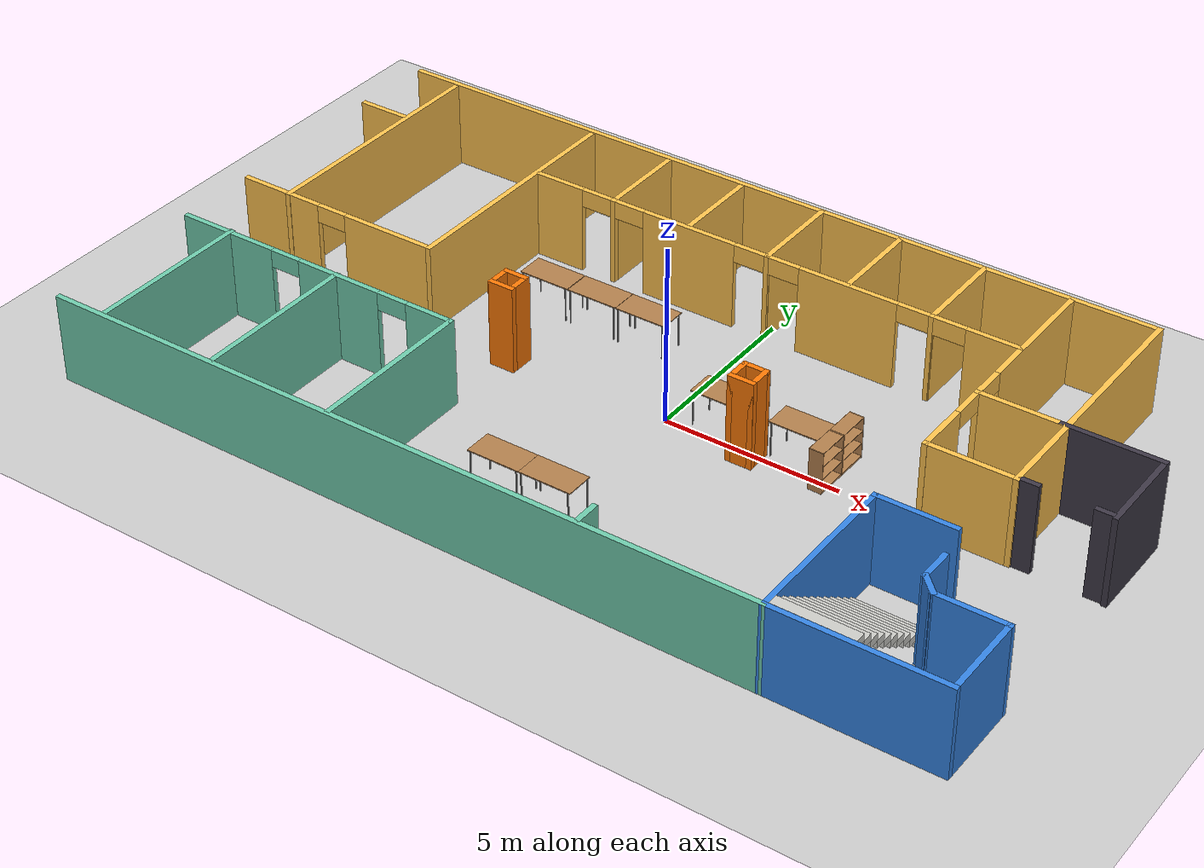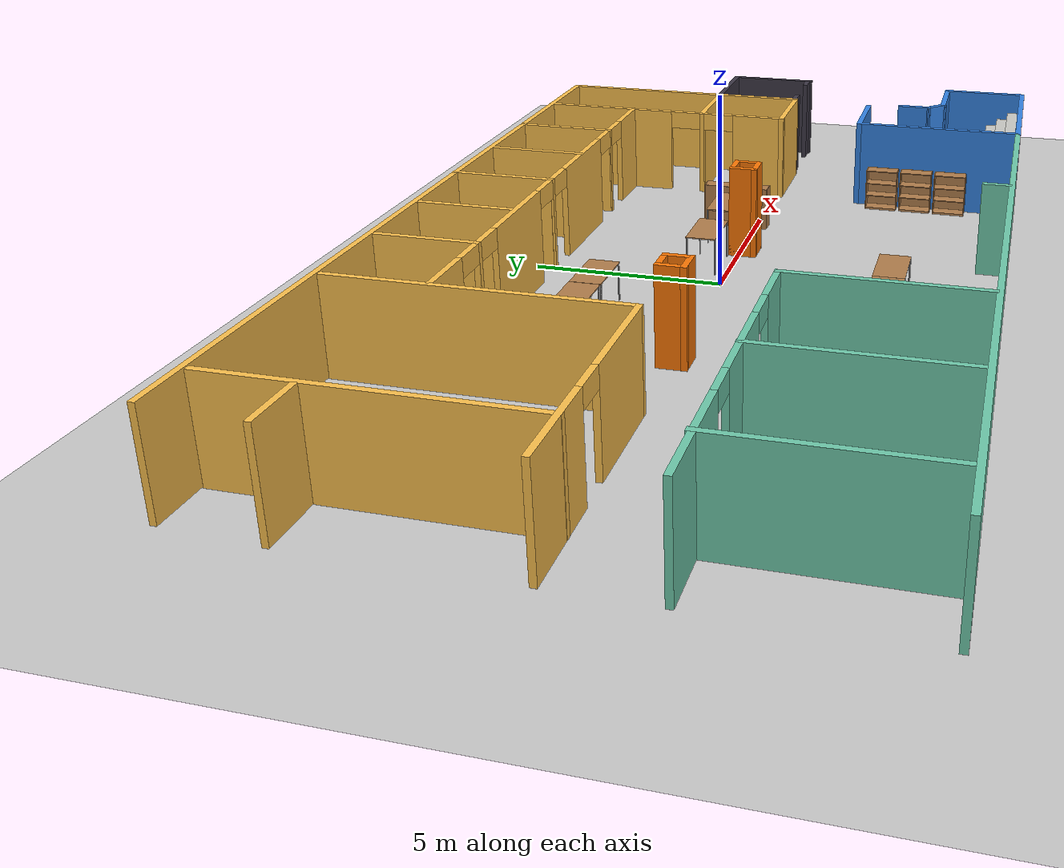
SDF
<sdf version="1.7">
 <world name="default">
  <light name="sun" type="directional">
   <pose>0 0 10 0 -0 0</pose>
   <diffuse>0.8 0.8 0.8 1</diffuse>
   <specular>0.2 0.2 0.2 1</specular>
   <attenuation>
    <range>1000</range>
    <constant>0.9</constant>
    <linear>0.01</linear>
    <quadratic>0.001</quadratic>
   </attenuation>
   <direction>-0.5 0.1 -0.9</direction>
   <spot><inner_angle>0</inner_angle><outer_angle>0</outer_angle><falloff>0</falloff></spot>
  </light>
  <model name="ground_plane">
   <static>1</static>
   <link name="link">
    <collision name="collision">
     <geometry><plane><normal>0 0 1</normal><size>100 100</size></plane></geometry>
     <surface>
      <contact><collide_bitmask>65535</collide_bitmask></contact>
      <friction><ode><mu>100</mu><mu2>50</mu2></ode></friction>
     </surface>
    </collision>
    <visual name="visual">
     <cast_shadows>0</cast_shadows>
     <geometry><plane><normal>0 0 1</normal><size>100 100</size></plane></geometry>
     <material>
      <script><uri>file://media/materials/scripts/gazebo.material</uri><name>Gazebo/Grey</name></script>
     </material>
    </visual>
   </link>
  </model>
  <gravity>0 0 -9.8</gravity>
  <magnetic_field>6e-06 2.3e-05 -4.2e-05</magnetic_field>
  <atmosphere type="adiabatic"/>
  <physics type="ode">
   <max_step_size>0.001</max_step_size>
   <real_time_factor>1</real_time_factor>
   <real_time_update_rate>1000</real_time_update_rate>
  </physics>
  <scene><ambient>0.4 0.4 0.4 1</ambient><background>0.7 0.7 0.7 1</background><shadows>1</shadows></scene>
  <spherical_coordinates>
   <surface_model>EARTH_WGS84</surface_model>
   <latitude_deg>0</latitude_deg>
   <longitude_deg>0</longitude_deg>
   <elevation>0</elevation>
   <heading_deg>0</heading_deg>
  </spherical_coordinates>
  <audio><device>default</device></audio>
  <model name="HUMEA_LABF">
   <pose>-0.653403 0.039249 0 0 -0 0</pose>
   <link name="Stairs_2">
    <visual name="Stairs_2_Visual_0">
     <pose>9.09481 -3.61254 0.104167 0 -0 0</pose>
     <geometry><box><size>2.18072 0.301964 0.208333</size></box></geometry>
     <material>
      <script><uri>file://media/materials/scripts/gazebo.material</uri><name>Gazebo/CeilingTiled</name></script>
      <ambient>0.964706 0.827451 0.176471 1</ambient>
     </material>
     <meta><layer>0</layer></meta>
    </visual>
    <collision name="Stairs_2_Collision_0">
     <geometry><box><size>2.18072 0.301964 0.208333</size></box></geometry>
     <pose>9.09481 -3.61254 0.104167 0 -0 0</pose>
    </collision>
    <visual name="Stairs_2_Visual_1">
     <pose>9.09481 -3.91451 0.3125 0 -0 0</pose>
     <geometry><box><size>2.18072 0.301964 0.208333</size></box></geometry>
     <material>
      <script><uri>file://media/materials/scripts/gazebo.material</uri><name>Gazebo/CeilingTiled</name></script>
      <ambient>0.964706 0.827451 0.176471 1</ambient>
     </material>
     <meta><layer>0</layer></meta>
    </visual>
    <collision name="Stairs_2_Collision_1">
     <geometry><box><size>2.18072 0.301964 0.208333</size></box></geometry>
     <pose>9.09481 -3.91451 0.3125 0 -0 0</pose>
    </collision>
    <visual name="Stairs_2_Visual_2">
     <pose>9.09481 -4.21647 0.520833 0 -0 0</pose>
     <geometry><box><size>2.18072 0.301964 0.208333</size></box></geometry>
     <material>
      <script><uri>file://media/materials/scripts/gazebo.material</uri><name>Gazebo/CeilingTiled</name></script>
      <ambient>0.964706 0.827451 0.176471 1</ambient>
     </material>
     <meta><layer>0</layer></meta>
    </visual>
    <collision name="Stairs_2_Collision_2">
     <geometry><box><size>2.18072 0.301964 0.208333</size></box></geometry>
     <pose>9.09481 -4.21647 0.520833 0 -0 0</pose>
    </collision>
    <visual name="Stairs_2_Visual_3">
     <pose>9.09481 -4.51844 0.729167 0 -0 0</pose>
     <geometry><box><size>2.18072 0.301964 0.208333</size></box></geometry>
     <material>
      <script><uri>file://media/materials/scripts/gazebo.material</uri><name>Gazebo/CeilingTiled</name></script>
      <ambient>0.964706 0.827451 0.176471 1</ambient>
     </material>
     <meta><layer>0</layer></meta>
    </visual>
    <collision name="Stairs_2_Collision_3">
     <geometry><box><size>2.18072 0.301964 0.208333</size></box></geometry>
     <pose>9.09481 -4.51844 0.729167 0 -0 0</pose>
    </collision>
    <visual name="Stairs_2_Visual_4">
     <pose>9.09481 -4.8204 0.9375 0 -0 0</pose>
     <geometry><box><size>2.18072 0.301964 0.208333</size></box></geometry>
     <material>
      <script><uri>file://media/materials/scripts/gazebo.material</uri><name>Gazebo/CeilingTiled</name></script>
      <ambient>0.964706 0.827451 0.176471 1</ambient>
     </material>
     <meta><layer>0</layer></meta>
    </visual>
    <collision name="Stairs_2_Collision_4">
     <geometry><box><size>2.18072 0.301964 0.208333</size></box></geometry>
     <pose>9.09481 -4.8204 0.9375 0 -0 0</pose>
    </collision>
    <visual name="Stairs_2_Visual_5">
     <pose>9.09481 -5.12236 1.14583 0 -0 0</pose>
     <geometry><box><size>2.18072 0.301964 0.208333</size></box></geometry>
     <material>
      <script><uri>file://media/materials/scripts/gazebo.material</uri><name>Gazebo/CeilingTiled</name></script>
      <ambient>0.964706 0.827451 0.176471 1</ambient>
     </material>
     <meta><layer>0</layer></meta>
    </visual>
    <collision name="Stairs_2_Collision_5">
     <geometry><box><size>2.18072 0.301964 0.208333</size></box></geometry>
     <pose>9.09481 -5.12236 1.14583 0 -0 0</pose>
    </collision>
    <visual name="Stairs_2_Visual_6">
     <pose>9.09481 -5.42433 1.35417 0 -0 0</pose>
     <geometry><box><size>2.18072 0.301964 0.208333</size></box></geometry>
     <material>
      <script><uri>file://media/materials/scripts/gazebo.material</uri><name>Gazebo/CeilingTiled</name></script>
      <ambient>0.964706 0.827451 0.176471 1</ambient>
     </material>
     <meta><layer>0</layer></meta>
    </visual>
    <collision name="Stairs_2_Collision_6">
     <geometry><box><size>2.18072 0.301964 0.208333</size></box></geometry>
     <pose>9.09481 -5.42433 1.35417 0 -0 0</pose>
    </collision>
    <visual name="Stairs_2_Visual_7">
     <pose>9.09481 -5.72629 1.5625 0 -0 0</pose>
     <geometry><box><size>2.18072 0.301964 0.208333</size></box></geometry>
     <material>
      <script><uri>file://media/materials/scripts/gazebo.material</uri><name>Gazebo/CeilingTiled</name></script>
      <ambient>0.964706 0.827451 0.176471 1</ambient>
     </material>
     <meta><layer>0</layer></meta>
    </visual>
    <collision name="Stairs_2_Collision_7">
     <geometry><box><size>2.18072 0.301964 0.208333</size></box></geometry>
     <pose>9.09481 -5.72629 1.5625 0 -0 0</pose>
    </collision>
    <visual name="Stairs_2_Visual_8">
     <pose>9.09481 -6.02826 1.77083 0 -0 0</pose>
     <geometry><box><size>2.18072 0.301964 0.208333</size></box></geometry>
     <material>
      <script><uri>file://media/materials/scripts/gazebo.material</uri><name>Gazebo/CeilingTiled</name></script>
      <ambient>0.964706 0.827451 0.176471 1</ambient>
     </material>
     <meta><layer>0</layer></meta>
    </visual>
    <collision name="Stairs_2_Collision_8">
     <geometry><box><size>2.18072 0.301964 0.208333</size></box></geometry>
     <pose>9.09481 -6.02826 1.77083 0 -0 0</pose>
    </collision>
    <visual name="Stairs_2_Visual_9">
     <pose>9.09481 -6.33022 1.97917 0 -0 0</pose>
     <geometry><box><size>2.18072 0.301964 0.208333</size></box></geometry>
     <material>
      <script><uri>file://media/materials/scripts/gazebo.material</uri><name>Gazebo/CeilingTiled</name></script>
      <ambient>0.964706 0.827451 0.176471 1</ambient>
     </material>
     <meta><layer>0</layer></meta>
    </visual>
    <collision name="Stairs_2_Collision_9">
     <geometry><box><size>2.18072 0.301964 0.208333</size></box></geometry>
     <pose>9.09481 -6.33022 1.97917 0 -0 0</pose>
    </collision>
    <visual name="Stairs_2_Visual_10">
     <pose>9.09481 -6.63218 2.1875 0 -0 0</pose>
     <geometry><box><size>2.18072 0.301964 0.208333</size></box></geometry>
     <material>
      <script><uri>file://media/materials/scripts/gazebo.material</uri><name>Gazebo/CeilingTiled</name></script>
      <ambient>0.964706 0.827451 0.176471 1</ambient>
     </material>
     <meta><layer>0</layer></meta>
    </visual>
    <collision name="Stairs_2_Collision_10">
     <geometry><box><size>2.18072 0.301964 0.208333</size></box></geometry>
     <pose>9.09481 -6.63218 2.1875 0 -0 0</pose>
    </collision>
    <visual name="Stairs_2_Visual_11">
     <pose>9.09481 -6.93415 2.39583 0 -0 0</pose>
     <geometry><box><size>2.18072 0.301964 0.208333</size></box></geometry>
     <material>
      <script><uri>file://media/materials/scripts/gazebo.material</uri><name>Gazebo/CeilingTiled</name></script>
      <ambient>0.964706 0.827451 0.176471 1</ambient>
     </material>
     <meta><layer>0</layer></meta>
    </visual>
    <collision name="Stairs_2_Collision_11">
     <geometry><box><size>2.18072 0.301964 0.208333</size></box></geometry>
     <pose>9.09481 -6.93415 2.39583 0 -0 0</pose>
    </collision>
   </link>
   <link name="Wall_10">
    <pose>-9.62585 -0.121188 0 0 -0 0</pose>
    <visual name="Wall_10_Visual_0">
     <pose>-1.866 0 1.25 0 -0 0</pose>
     <geometry><box><size>2.51799 0.15 2.5</size></box></geometry>
     <material>
      <script><uri>file://media/materials/scripts/gazebo.material</uri><name>Gazebo/Grey</name></script>
      <ambient>1 0.764706 0.305882 1</ambient>
     </material>
     <meta><layer>0</layer></meta>
    </visual>
    <collision name="Wall_10_Collision_0">
     <geometry><box><size>2.51799 0.15 2.5</size></box></geometry>
     <pose>-1.866 0 1.25 0 -0 0</pose>
    </collision>
    <visual name="Wall_10_Visual_1">
     <pose>1.709 0 1.25 0 -0 0</pose>
     <geometry><box><size>2.83201 0.15 2.5</size></box></geometry>
     <material>
      <script><uri>file://media/materials/scripts/gazebo.material</uri><name>Gazebo/Grey</name></script>
      <ambient>1 0.764706 0.305882 1</ambient>
     </material>
     <meta><layer>0</layer></meta>
    </visual>
    <collision name="Wall_10_Collision_1">
     <geometry><box><size>2.83201 0.15 2.5</size></box></geometry>
     <pose>1.709 0 1.25 0 -0 0</pose>
    </collision>
    <visual name="Wall_10_Visual_2">
     <pose>-0.157006 0 2.25 0 -0 0</pose>
     <geometry><box><size>0.9 0.15 0.5</size></box></geometry>
     <material>
      <script><uri>file://media/materials/scripts/gazebo.material</uri><name>Gazebo/Grey</name></script>
      <ambient>1 0.764706 0.305882 1</ambient>
     </material>
     <meta><layer>0</layer></meta>
    </visual>
    <collision name="Wall_10_Collision_2">
     <geometry><box><size>0.9 0.15 0.5</size></box></geometry>
     <pose>-0.157006 0 2.25 0 -0 0</pose>
    </collision>
   </link>
   <link name="Wall_11">
    <collision name="Wall_11_Collision">
     <geometry><box><size>7.25 0.15 2.5</size></box></geometry>
     <pose>0 0 1.25 0 -0 0</pose>
    </collision>
    <visual name="Wall_11_Visual">
     <pose>0 0 1.25 0 -0 0</pose>
     <geometry><box><size>7.25 0.15 2.5</size></box></geometry>
     <material>
      <script><uri>file://media/materials/scripts/gazebo.material</uri><name>Gazebo/Grey</name></script>
      <ambient>1 0.764706 0.305882 1</ambient>
     </material>
     <meta><layer>0</layer></meta>
    </visual>
    <pose>-6.57585 3.42881 0 0 -0 1.5708</pose>
   </link>
   <link name="Wall_13">
    <collision name="Wall_13_Collision">
     <geometry><box><size>1.5 0.15 2.5</size></box></geometry>
     <pose>0 0 1.25 0 -0 0</pose>
    </collision>
    <visual name="Wall_13_Visual">
     <pose>0 0 1.25 0 -0 0</pose>
     <geometry><box><size>1.5 0.15 2.5</size></box></geometry>
     <material>
      <script><uri>file://media/materials/scripts/gazebo.material</uri><name>Gazebo/Grey</name></script>
      <ambient>1 0.764706 0.305882 1</ambient>
     </material>
     <meta><layer>0</layer></meta>
    </visual>
    <pose>-12.0496 4.82333 0 0 -0 0</pose>
   </link>
   <link name="Wall_15">
    <pose>0.709218 4.49976 0 0 -0 0</pose>
    <visual name="Wall_15_Visual_0">
     <pose>-6.50165 0 1.25 0 -0 0</pose>
     <geometry><box><size>1.4967 0.15 2.5</size></box></geometry>
     <material>
      <script><uri>file://media/materials/scripts/gazebo.material</uri><name>Gazebo/Grey</name></script>
      <ambient>1 0.764706 0.305882 1</ambient>
     </material>
     <meta><layer>0</layer></meta>
    </visual>
    <collision name="Wall_15_Collision_0">
     <geometry><box><size>1.4967 0.15 2.5</size></box></geometry>
     <pose>-6.50165 0 1.25 0 -0 0</pose>
    </collision>
    <visual name="Wall_15_Visual_1">
     <pose>-4.7792 0 1.25 0 -0 0</pose>
     <geometry><box><size>0.148204 0.15 2.5</size></box></geometry>
     <material>
      <script><uri>file://media/materials/scripts/gazebo.material</uri><name>Gazebo/Grey</name></script>
      <ambient>1 0.764706 0.305882 1</ambient>
     </material>
     <meta><layer>0</layer></meta>
    </visual>
    <collision name="Wall_15_Collision_1">
     <geometry><box><size>0.148204 0.15 2.5</size></box></geometry>
     <pose>-4.7792 0 1.25 0 -0 0</pose>
    </collision>
    <visual name="Wall_15_Visual_2">
     <pose>-2.40226 0 1.25 0 -0 0</pose>
     <geometry><box><size>2.80567 0.15 2.5</size></box></geometry>
     <material>
      <script><uri>file://media/materials/scripts/gazebo.material</uri><name>Gazebo/Grey</name></script>
      <ambient>1 0.764706 0.305882 1</ambient>
     </material>
     <meta><layer>0</layer></meta>
    </visual>
    <collision name="Wall_15_Collision_2">
     <geometry><box><size>2.80567 0.15 2.5</size></box></geometry>
     <pose>-2.40226 0 1.25 0 -0 0</pose>
    </collision>
    <visual name="Wall_15_Visual_3">
     <pose>-0.032372 0 1.25 0 -0 0</pose>
     <geometry><box><size>0.134115 0.15 2.5</size></box></geometry>
     <material>
      <script><uri>file://media/materials/scripts/gazebo.material</uri><name>Gazebo/Grey</name></script>
      <ambient>1 0.764706 0.305882 1</ambient>
     </material>
     <meta><layer>0</layer></meta>
    </visual>
    <collision name="Wall_15_Collision_3">
     <geometry><box><size>0.134115 0.15 2.5</size></box></geometry>
     <pose>-0.032372 0 1.25 0 -0 0</pose>
    </collision>
    <visual name="Wall_15_Visual_4">
     <pose>2.35489 0 1.25 0 -0 0</pose>
     <geometry><box><size>2.84041 0.15 2.5</size></box></geometry>
     <material>
      <script><uri>file://media/materials/scripts/gazebo.material</uri><name>Gazebo/Grey</name></script>
      <ambient>1 0.764706 0.305882 1</ambient>
     </material>
     <meta><layer>0</layer></meta>
    </visual>
    <collision name="Wall_15_Collision_4">
     <geometry><box><size>2.84041 0.15 2.5</size></box></geometry>
     <pose>2.35489 0 1.25 0 -0 0</pose>
    </collision>
    <visual name="Wall_15_Visual_5">
     <pose>4.73861 0 1.25 0 -0 0</pose>
     <geometry><box><size>0.127028 0.15 2.5</size></box></geometry>
     <material>
      <script><uri>file://media/materials/scripts/gazebo.material</uri><name>Gazebo/Grey</name></script>
      <ambient>1 0.764706 0.305882 1</ambient>
     </material>
     <meta><layer>0</layer></meta>
    </visual>
    <collision name="Wall_15_Collision_5">
     <geometry><box><size>0.127028 0.15 2.5</size></box></geometry>
     <pose>4.73861 0 1.25 0 -0 0</pose>
    </collision>
    <visual name="Wall_15_Visual_6">
     <pose>6.47606 0 1.25 0 -0 0</pose>
     <geometry><box><size>1.54787 0.15 2.5</size></box></geometry>
     <material>
      <script><uri>file://media/materials/scripts/gazebo.material</uri><name>Gazebo/Grey</name></script>
      <ambient>1 0.764706 0.305882 1</ambient>
     </material>
     <meta><layer>0</layer></meta>
    </visual>
    <collision name="Wall_15_Collision_6">
     <geometry><box><size>1.54787 0.15 2.5</size></box></geometry>
     <pose>6.47606 0 1.25 0 -0 0</pose>
    </collision>
    <visual name="Wall_15_Visual_7">
     <pose>-5.3033 0 2.25 0 -0 0</pose>
     <geometry><box><size>0.9 0.15 0.5</size></box></geometry>
     <material>
      <script><uri>file://media/materials/scripts/gazebo.material</uri><name>Gazebo/Grey</name></script>
      <ambient>1 0.764706 0.305882 1</ambient>
     </material>
     <meta><layer>0</layer></meta>
    </visual>
    <collision name="Wall_15_Collision_7">
     <geometry><box><size>0.9 0.15 0.5</size></box></geometry>
     <pose>-5.3033 0 2.25 0 -0 0</pose>
    </collision>
    <visual name="Wall_15_Visual_8">
     <pose>-4.2551 0 2.25 0 -0 0</pose>
     <geometry><box><size>0.9 0.15 0.5</size></box></geometry>
     <material>
      <script><uri>file://media/materials/scripts/gazebo.material</uri><name>Gazebo/Grey</name></script>
      <ambient>1 0.764706 0.305882 1</ambient>
     </material>
     <meta><layer>0</layer></meta>
    </visual>
    <collision name="Wall_15_Collision_8">
     <geometry><box><size>0.9 0.15 0.5</size></box></geometry>
     <pose>-4.2551 0 2.25 0 -0 0</pose>
    </collision>
    <visual name="Wall_15_Visual_9">
     <pose>-0.54943 0 2.25 0 -0 0</pose>
     <geometry><box><size>0.9 0.15 0.5</size></box></geometry>
     <material>
      <script><uri>file://media/materials/scripts/gazebo.material</uri><name>Gazebo/Grey</name></script>
      <ambient>1 0.764706 0.305882 1</ambient>
     </material>
     <meta><layer>0</layer></meta>
    </visual>
    <collision name="Wall_15_Collision_9">
     <geometry><box><size>0.9 0.15 0.5</size></box></geometry>
     <pose>-0.54943 0 2.25 0 -0 0</pose>
    </collision>
    <visual name="Wall_15_Visual_10">
     <pose>0.484685 0 2.25 0 -0 0</pose>
     <geometry><box><size>0.9 0.15 0.5</size></box></geometry>
     <material>
      <script><uri>file://media/materials/scripts/gazebo.material</uri><name>Gazebo/Grey</name></script>
      <ambient>1 0.764706 0.305882 1</ambient>
     </material>
     <meta><layer>0</layer></meta>
    </visual>
    <collision name="Wall_15_Collision_10">
     <geometry><box><size>0.9 0.15 0.5</size></box></geometry>
     <pose>0.484685 0 2.25 0 -0 0</pose>
    </collision>
    <visual name="Wall_15_Visual_11">
     <pose>4.2251 0 2.25 0 -0 0</pose>
     <geometry><box><size>0.9 0.15 0.5</size></box></geometry>
     <material>
      <script><uri>file://media/materials/scripts/gazebo.material</uri><name>Gazebo/Grey</name></script>
      <ambient>1 0.764706 0.305882 1</ambient>
     </material>
     <meta><layer>0</layer></meta>
    </visual>
    <collision name="Wall_15_Collision_11">
     <geometry><box><size>0.9 0.15 0.5</size></box></geometry>
     <pose>4.2251 0 2.25 0 -0 0</pose>
    </collision>
    <visual name="Wall_15_Visual_12">
     <pose>5.25213 0 2.25 0 -0 0</pose>
     <geometry><box><size>0.9 0.15 0.5</size></box></geometry>
     <material>
      <script><uri>file://media/materials/scripts/gazebo.material</uri><name>Gazebo/Grey</name></script>
      <ambient>1 0.764706 0.305882 1</ambient>
     </material>
     <meta><layer>0</layer></meta>
    </visual>
    <collision name="Wall_15_Collision_12">
     <geometry><box><size>0.9 0.15 0.5</size></box></geometry>
     <pose>5.25213 0 2.25 0 -0 0</pose>
    </collision>
   </link>
   <link name="Wall_17">
    <collision name="Wall_17_Collision">
     <geometry><box><size>2.5 0.15 2.5</size></box></geometry>
     <pose>0 0 1.25 0 -0 0</pose>
    </collision>
    <visual name="Wall_17_Visual">
     <pose>0 0 1.25 0 -0 0</pose>
     <geometry><box><size>2.5 0.15 2.5</size></box></geometry>
     <material>
      <script><uri>file://media/materials/scripts/gazebo.material</uri><name>Gazebo/Grey</name></script>
      <ambient>1 0.764706 0.305882 1</ambient>
     </material>
     <meta><layer>0</layer></meta>
    </visual>
    <pose>-4.06326 5.823 0 0 -0 -1.5708</pose>
   </link>
   <link name="Wall_19">
    <collision name="Wall_19_Collision">
     <geometry><box><size>2.5 0.15 2.5</size></box></geometry>
     <pose>0 0 1.25 0 -0 0</pose>
    </collision>
    <visual name="Wall_19_Visual">
     <pose>0 0 1.25 0 -0 0</pose>
     <geometry><box><size>2.5 0.15 2.5</size></box></geometry>
     <material>
      <script><uri>file://media/materials/scripts/gazebo.material</uri><name>Gazebo/Grey</name></script>
      <ambient>1 0.764706 0.305882 1</ambient>
     </material>
     <meta><layer>0</layer></meta>
    </visual>
    <pose>-1.74687 5.8141 0 0 -0 -1.5708</pose>
   </link>
   <link name="Wall_21">
    <collision name="Wall_21_Collision">
     <geometry><box><size>2.75 0.15 2.5</size></box></geometry>
     <pose>0 0 1.25 0 -0 0</pose>
    </collision>
    <visual name="Wall_21_Visual">
     <pose>0 0 1.25 0 -0 0</pose>
     <geometry><box><size>2.75 0.15 2.5</size></box></geometry>
     <material>
      <script><uri>file://media/materials/scripts/gazebo.material</uri><name>Gazebo/Grey</name></script>
      <ambient>1 0.764706 0.305882 1</ambient>
     </material>
     <meta><layer>0</layer></meta>
    </visual>
    <pose>0.678051 5.86584 0 0 -0 -1.5708</pose>
   </link>
   <link name="Wall_23">
    <collision name="Wall_23_Collision">
     <geometry><box><size>2.75 0.15 2.5</size></box></geometry>
     <pose>0 0 1.25 0 -0 0</pose>
    </collision>
    <visual name="Wall_23_Visual">
     <pose>0 0 1.25 0 -0 0</pose>
     <geometry><box><size>2.75 0.15 2.5</size></box></geometry>
     <material>
      <script><uri>file://media/materials/scripts/gazebo.material</uri><name>Gazebo/Grey</name></script>
      <ambient>1 0.764706 0.305882 1</ambient>
     </material>
     <meta><layer>0</layer></meta>
    </visual>
    <pose>3.02991 5.83125 0 0 -0 -1.5708</pose>
   </link>
   <link name="Wall_25">
    <collision name="Wall_25_Collision">
     <geometry><box><size>2.75 0.15 2.5</size></box></geometry>
     <pose>0 0 1.25 0 -0 0</pose>
    </collision>
    <visual name="Wall_25_Visual">
     <pose>0 0 1.25 0 -0 0</pose>
     <geometry><box><size>2.75 0.15 2.5</size></box></geometry>
     <material>
      <script><uri>file://media/materials/scripts/gazebo.material</uri><name>Gazebo/Grey</name></script>
      <ambient>1 0.764706 0.305882 1</ambient>
     </material>
     <meta><layer>0</layer></meta>
    </visual>
    <pose>5.45555 5.83943 0 0 -0 -1.5708</pose>
   </link>
   <link name="Wall_27">
    <collision name="Wall_27_Collision">
     <geometry><box><size>2.25 0.15 2.5</size></box></geometry>
     <pose>0 0 1.25 0 -0 0</pose>
    </collision>
    <visual name="Wall_27_Visual">
     <pose>0 0 1.25 0 -0 0</pose>
     <geometry><box><size>2.25 0.15 2.5</size></box></geometry>
     <material>
      <script><uri>file://media/materials/scripts/gazebo.material</uri><name>Gazebo/Grey</name></script>
      <ambient>1 0.764706 0.305882 1</ambient>
     </material>
     <meta><layer>0</layer></meta>
    </visual>
    <pose>9.07464 2.29514 0 0 -0 3.14159</pose>
   </link>
   <link name="Wall_29">
    <pose>-8.3773 -2.46976 0 0 -0 0</pose>
    <visual name="Wall_29_Visual_0">
     <pose>-2.89279 0 1.25 0 -0 0</pose>
     <geometry><box><size>2.96442 0.15 2.5</size></box></geometry>
     <material>
      <script><uri>file://media/materials/scripts/gazebo.material</uri><name>Gazebo/Grey</name></script>
      <ambient>0.435294 0.796078 0.67451 1</ambient>
     </material>
     <meta><layer>0</layer></meta>
    </visual>
    <collision name="Wall_29_Collision_0">
     <geometry><box><size>2.96442 0.15 2.5</size></box></geometry>
     <pose>-2.89279 0 1.25 0 -0 0</pose>
    </collision>
    <visual name="Wall_29_Visual_1">
     <pose>0.769166 0 1.25 0 -0 0</pose>
     <geometry><box><size>2.5595 0.15 2.5</size></box></geometry>
     <material>
      <script><uri>file://media/materials/scripts/gazebo.material</uri><name>Gazebo/Grey</name></script>
      <ambient>0.435294 0.796078 0.67451 1</ambient>
     </material>
     <meta><layer>0</layer></meta>
    </visual>
    <collision name="Wall_29_Collision_1">
     <geometry><box><size>2.5595 0.15 2.5</size></box></geometry>
     <pose>0.769166 0 1.25 0 -0 0</pose>
    </collision>
    <visual name="Wall_29_Visual_2">
     <pose>3.66196 0 1.25 0 -0 0</pose>
     <geometry><box><size>1.42608 0.15 2.5</size></box></geometry>
     <material>
      <script><uri>file://media/materials/scripts/gazebo.material</uri><name>Gazebo/Grey</name></script>
      <ambient>0.435294 0.796078 0.67451 1</ambient>
     </material>
     <meta><layer>0</layer></meta>
    </visual>
    <collision name="Wall_29_Collision_2">
     <geometry><box><size>1.42608 0.15 2.5</size></box></geometry>
     <pose>3.66196 0 1.25 0 -0 0</pose>
    </collision>
    <visual name="Wall_29_Visual_3">
     <pose>-0.960584 0 2.25 0 -0 0</pose>
     <geometry><box><size>0.9 0.15 0.5</size></box></geometry>
     <material>
      <script><uri>file://media/materials/scripts/gazebo.material</uri><name>Gazebo/Grey</name></script>
      <ambient>0.435294 0.796078 0.67451 1</ambient>
     </material>
     <meta><layer>0</layer></meta>
    </visual>
    <collision name="Wall_29_Collision_3">
     <geometry><box><size>0.9 0.15 0.5</size></box></geometry>
     <pose>-0.960584 0 2.25 0 -0 0</pose>
    </collision>
    <visual name="Wall_29_Visual_4">
     <pose>2.49892 0 2.25 0 -0 0</pose>
     <geometry><box><size>0.9 0.15 0.5</size></box></geometry>
     <material>
      <script><uri>file://media/materials/scripts/gazebo.material</uri><name>Gazebo/Grey</name></script>
      <ambient>0.435294 0.796078 0.67451 1</ambient>
     </material>
     <meta><layer>0</layer></meta>
    </visual>
    <collision name="Wall_29_Collision_4">
     <geometry><box><size>0.9 0.15 0.5</size></box></geometry>
     <pose>2.49892 0 2.25 0 -0 0</pose>
    </collision>
   </link>
   <link name="Wall_3">
    <collision name="Wall_3_Collision">
     <geometry><box><size>22.9807 0.15 2.5</size></box></geometry>
     <pose>0 0 1.25 0 -0 0</pose>
    </collision>
    <visual name="Wall_3_Visual">
     <pose>0 0 1.25 0 -0 0</pose>
     <geometry><box><size>22.9807 0.15 2.5</size></box></geometry>
     <material>
      <script><uri>file://media/materials/scripts/gazebo.material</uri><name>Gazebo/Grey</name></script>
      <ambient>1 0.764706 0.305882 1</ambient>
     </material>
     <meta><layer>0</layer></meta>
    </visual>
    <pose>-1.17346 7.15775 0 0 -0 0</pose>
   </link>
   <link name="Wall_30">
    <collision name="Wall_30_Collision">
     <geometry><box><size>4.75 0.15 2.5</size></box></geometry>
     <pose>0 0 1.25 0 -0 0</pose>
    </collision>
    <visual name="Wall_30_Visual">
     <pose>0 0 1.25 0 -0 0</pose>
     <geometry><box><size>4.75 0.15 2.5</size></box></geometry>
     <material>
      <script><uri>file://media/materials/scripts/gazebo.material</uri><name>Gazebo/Grey</name></script>
      <ambient>0.435294 0.796078 0.67451 1</ambient>
     </material>
     <meta><layer>0</layer></meta>
    </visual>
    <pose>-4.0773 -4.76976 0 0 -0 -1.5708</pose>
   </link>
   <link name="Wall_35">
    <collision name="Wall_35_Collision">
     <geometry><box><size>20.75 0.15 2.5</size></box></geometry>
     <pose>0 0 1.25 0 -0 0</pose>
    </collision>
    <visual name="Wall_35_Visual">
     <pose>0 0 1.25 0 -0 0</pose>
     <geometry><box><size>20.75 0.15 2.5</size></box></geometry>
     <material>
      <script><uri>file://media/materials/scripts/gazebo.material</uri><name>Gazebo/Grey</name></script>
      <ambient>0.435294 0.796078 0.67451 1</ambient>
     </material>
     <meta><layer>0</layer></meta>
    </visual>
    <pose>-2.35433 -7.16563 0 0 -0 3.14159</pose>
   </link>
   <link name="Wall_37">
    <collision name="Wall_37_Collision">
     <geometry><box><size>4.75 0.15 2.5</size></box></geometry>
     <pose>0 0 1.25 0 -0 0</pose>
    </collision>
    <visual name="Wall_37_Visual">
     <pose>0 0 1.25 0 -0 0</pose>
     <geometry><box><size>4.75 0.15 2.5</size></box></geometry>
     <material>
      <script><uri>file://media/materials/scripts/gazebo.material</uri><name>Gazebo/Grey</name></script>
      <ambient>0.207843 0.517647 0.894118 1</ambient>
     </material>
     <meta><layer>0</layer></meta>
    </visual>
    <pose>7.94567 -4.86564 0 0 -0 -1.5708</pose>
   </link>
   <link name="Wall_4">
    <collision name="Wall_4_Collision">
     <geometry><box><size>7.48904 0.15 2.5</size></box></geometry>
     <pose>0 0 1.25 0 -0 0</pose>
    </collision>
    <visual name="Wall_4_Visual">
     <pose>0 0 1.25 0 -0 0</pose>
     <geometry><box><size>7.48904 0.15 2.5</size></box></geometry>
     <material>
      <script><uri>file://media/materials/scripts/gazebo.material</uri><name>Gazebo/Grey</name></script>
      <ambient>1 0.764706 0.305882 1</ambient>
     </material>
     <meta><layer>0</layer></meta>
    </visual>
    <pose>10.2612 3.48823 0 0 -0 -1.5708</pose>
   </link>
   <link name="Wall_41">
    <collision name="Wall_41_Collision">
     <geometry><box><size>2.25 0.15 2.5</size></box></geometry>
     <pose>0 0 1.25 0 -0 0</pose>
    </collision>
    <visual name="Wall_41_Visual">
     <pose>0 0 1.25 0 -0 0</pose>
     <geometry><box><size>2.25 0.15 2.5</size></box></geometry>
     <material>
      <script><uri>file://media/materials/scripts/gazebo.material</uri><name>Gazebo/Grey</name></script>
      <ambient>0.207843 0.517647 0.894118 1</ambient>
     </material>
     <meta><layer>0</layer></meta>
    </visual>
    <pose>8.99519 -2.54083 0 0 -0 3.14159</pose>
   </link>
   <link name="Wall_43">
    <collision name="Wall_43_Collision">
     <geometry><box><size>0.75 0.15 2.5</size></box></geometry>
     <pose>0 0 1.25 0 -0 0</pose>
    </collision>
    <visual name="Wall_43_Visual">
     <pose>0 0 1.25 0 -0 0</pose>
     <geometry><box><size>0.75 0.15 2.5</size></box></geometry>
     <material>
      <script><uri>file://media/materials/scripts/gazebo.material</uri><name>Gazebo/Grey</name></script>
      <ambient>0.435294 0.796078 0.67451 1</ambient>
     </material>
     <meta><layer>0</layer></meta>
    </visual>
    <pose>3.06146 -6.7839 0 0 -0 1.5708</pose>
   </link>
   <link name="Wall_45">
    <collision name="Wall_45_Collision">
     <geometry><box><size>0.75 0.15 2.5</size></box></geometry>
     <pose>0 0 1.25 0 -0 0</pose>
    </collision>
    <visual name="Wall_45_Visual">
     <pose>0 0 1.25 0 -0 0</pose>
     <geometry><box><size>0.75 0.15 2.5</size></box></geometry>
     <material>
      <script><uri>file://media/materials/scripts/gazebo.material</uri><name>Gazebo/Grey</name></script>
      <ambient>0.996078 0.47451 0.0196078 1</ambient>
     </material>
     <meta><layer>0</layer></meta>
    </visual>
    <pose>3.0974 0.142151 0 0 -0 0</pose>
   </link>
   <link name="Wall_46">
    <collision name="Wall_46_Collision">
     <geometry><box><size>0.75 0.15 2.5</size></box></geometry>
     <pose>0 0 1.25 0 -0 0</pose>
    </collision>
    <visual name="Wall_46_Visual">
     <pose>0 0 1.25 0 -0 0</pose>
     <geometry><box><size>0.75 0.15 2.5</size></box></geometry>
     <material>
      <script><uri>file://media/materials/scripts/gazebo.material</uri><name>Gazebo/Grey</name></script>
      <ambient>0.996078 0.47451 0.0196078 1</ambient>
     </material>
     <meta><layer>0</layer></meta>
    </visual>
    <pose>3.3974 -0.157849 0 0 -0 -1.5708</pose>
   </link>
   <link name="Wall_47">
    <collision name="Wall_47_Collision">
     <geometry><box><size>0.75 0.15 2.5</size></box></geometry>
     <pose>0 0 1.25 0 -0 0</pose>
    </collision>
    <visual name="Wall_47_Visual">
     <pose>0 0 1.25 0 -0 0</pose>
     <geometry><box><size>0.75 0.15 2.5</size></box></geometry>
     <material>
      <script><uri>file://media/materials/scripts/gazebo.material</uri><name>Gazebo/Grey</name></script>
      <ambient>0.996078 0.47451 0.0196078 1</ambient>
     </material>
     <meta><layer>0</layer></meta>
    </visual>
    <pose>3.0974 -0.457849 0 0 -0 3.14159</pose>
   </link>
   <link name="Wall_48">
    <collision name="Wall_48_Collision">
     <geometry><box><size>0.75 0.15 2.5</size></box></geometry>
     <pose>0 0 1.25 0 -0 0</pose>
    </collision>
    <visual name="Wall_48_Visual">
     <pose>0 0 1.25 0 -0 0</pose>
     <geometry><box><size>0.75 0.15 2.5</size></box></geometry>
     <material>
      <script><uri>file://media/materials/scripts/gazebo.material</uri><name>Gazebo/Grey</name></script>
      <ambient>0.996078 0.47451 0.0196078 1</ambient>
     </material>
     <meta><layer>0</layer></meta>
    </visual>
    <pose>2.7974 -0.157849 0 0 -0 1.5708</pose>
   </link>
   <link name="Wall_5">
    <collision name="Wall_5_Collision">
     <geometry><box><size>2.50001 0.15 2.5</size></box></geometry>
     <pose>0 0 1.25 0 -0 0</pose>
    </collision>
    <visual name="Wall_5_Visual">
     <pose>0 0 1.25 0 -0 0</pose>
     <geometry><box><size>2.50001 0.15 2.5</size></box></geometry>
     <material>
      <script><uri>file://media/materials/scripts/gazebo.material</uri><name>Gazebo/Grey</name></script>
      <ambient>1 0.764706 0.305882 1</ambient>
     </material>
     <meta><layer>0</layer></meta>
    </visual>
    <pose>9.08619 -0.181285 0 0 -0 3.14159</pose>
   </link>
   <link name="Wall_50">
    <collision name="Wall_50_Collision">
     <geometry><box><size>0.75 0.15 2.5</size></box></geometry>
     <pose>0 0 1.25 0 -0 0</pose>
    </collision>
    <visual name="Wall_50_Visual">
     <pose>0 0 1.25 0 -0 0</pose>
     <geometry><box><size>0.75 0.15 2.5</size></box></geometry>
     <material>
      <script><uri>file://media/materials/scripts/gazebo.material</uri><name>Gazebo/Grey</name></script>
      <ambient>0.996078 0.47451 0.0196078 1</ambient>
     </material>
     <meta><layer>0</layer></meta>
    </visual>
    <pose>-4.0293 0.148618 0 0 -0 0</pose>
   </link>
   <link name="Wall_51">
    <collision name="Wall_51_Collision">
     <geometry><box><size>0.75 0.15 2.5</size></box></geometry>
     <pose>0 0 1.25 0 -0 0</pose>
    </collision>
    <visual name="Wall_51_Visual">
     <pose>0 0 1.25 0 -0 0</pose>
     <geometry><box><size>0.75 0.15 2.5</size></box></geometry>
     <material>
      <script><uri>file://media/materials/scripts/gazebo.material</uri><name>Gazebo/Grey</name></script>
      <ambient>0.996078 0.47451 0.0196078 1</ambient>
     </material>
     <meta><layer>0</layer></meta>
    </visual>
    <pose>-3.7293 -0.151382 0 0 -0 -1.5708</pose>
   </link>
   <link name="Wall_52">
    <collision name="Wall_52_Collision">
     <geometry><box><size>0.75 0.15 2.5</size></box></geometry>
     <pose>0 0 1.25 0 -0 0</pose>
    </collision>
    <visual name="Wall_52_Visual">
     <pose>0 0 1.25 0 -0 0</pose>
     <geometry><box><size>0.75 0.15 2.5</size></box></geometry>
     <material>
      <script><uri>file://media/materials/scripts/gazebo.material</uri><name>Gazebo/Grey</name></script>
      <ambient>0.996078 0.47451 0.0196078 1</ambient>
     </material>
     <meta><layer>0</layer></meta>
    </visual>
    <pose>-4.0293 -0.451382 0 0 -0 3.14159</pose>
   </link>
   <link name="Wall_53">
    <collision name="Wall_53_Collision">
     <geometry><box><size>0.75 0.15 2.5</size></box></geometry>
     <pose>0 0 1.25 0 -0 0</pose>
    </collision>
    <visual name="Wall_53_Visual">
     <pose>0 0 1.25 0 -0 0</pose>
     <geometry><box><size>0.75 0.15 2.5</size></box></geometry>
     <material>
      <script><uri>file://media/materials/scripts/gazebo.material</uri><name>Gazebo/Grey</name></script>
      <ambient>0.996078 0.47451 0.0196078 1</ambient>
     </material>
     <meta><layer>0</layer></meta>
    </visual>
    <pose>-4.3293 -0.151382 0 0 -0 1.5708</pose>
   </link>
   <link name="Wall_55">
    <collision name="Wall_55_Collision">
     <geometry><box><size>4.75 0.15 2.5</size></box></geometry>
     <pose>0 0 1.25 0 -0 0</pose>
    </collision>
    <visual name="Wall_55_Visual">
     <pose>0 0 1.25 0 -0 0</pose>
     <geometry><box><size>4.75 0.15 2.5</size></box></geometry>
     <material>
      <script><uri>file://media/materials/scripts/gazebo.material</uri><name>Gazebo/Grey</name></script>
      <ambient>0.435294 0.796078 0.67451 1</ambient>
     </material>
     <meta><layer>0</layer></meta>
    </visual>
    <pose>-7.7074 -4.7567 0 0 -0 -1.5708</pose>
   </link>
   <link name="Wall_58">
    <collision name="Wall_58_Collision">
     <geometry><box><size>4.75 0.15 2.5</size></box></geometry>
     <pose>0 0 1.25 0 -0 0</pose>
    </collision>
    <visual name="Wall_58_Visual">
     <pose>0 0 1.25 0 -0 0</pose>
     <geometry><box><size>4.75 0.15 2.5</size></box></geometry>
     <material>
      <script><uri>file://media/materials/scripts/gazebo.material</uri><name>Gazebo/Grey</name></script>
      <ambient>0.435294 0.796078 0.67451 1</ambient>
     </material>
     <meta><layer>0</layer></meta>
    </visual>
    <pose>-11.2358 -4.72628 0 0 -0 -1.5708</pose>
   </link>
   <link name="Wall_6">
    <pose>7.91119 3.48549 0 0 -0 1.5708</pose>
    <visual name="Wall_6_Visual_0">
     <pose>-2.95664 0 1.25 0 -0 0</pose>
     <geometry><box><size>1.58124 0.15 2.5</size></box></geometry>
     <material>
      <script><uri>file://media/materials/scripts/gazebo.material</uri><name>Gazebo/Grey</name></script>
      <ambient>1 0.764706 0.305882 1</ambient>
     </material>
     <meta><layer>0</layer></meta>
    </visual>
    <collision name="Wall_6_Collision_0">
     <geometry><box><size>1.58124 0.15 2.5</size></box></geometry>
     <pose>-2.95664 0 1.25 0 -0 0</pose>
    </collision>
    <visual name="Wall_6_Visual_1">
     <pose>-1.19659 0 1.25 0 -0 0</pose>
     <geometry><box><size>0.138869 0.15 2.5</size></box></geometry>
     <material>
      <script><uri>file://media/materials/scripts/gazebo.material</uri><name>Gazebo/Grey</name></script>
      <ambient>1 0.764706 0.305882 1</ambient>
     </material>
     <meta><layer>0</layer></meta>
    </visual>
    <collision name="Wall_6_Collision_1">
     <geometry><box><size>0.138869 0.15 2.5</size></box></geometry>
     <pose>-1.19659 0 1.25 0 -0 0</pose>
    </collision>
    <visual name="Wall_6_Visual_2">
     <pose>1.76005 0 1.25 0 -0 0</pose>
     <geometry><box><size>3.97441 0.15 2.5</size></box></geometry>
     <material>
      <script><uri>file://media/materials/scripts/gazebo.material</uri><name>Gazebo/Grey</name></script>
      <ambient>1 0.764706 0.305882 1</ambient>
     </material>
     <meta><layer>0</layer></meta>
    </visual>
    <collision name="Wall_6_Collision_2">
     <geometry><box><size>3.97441 0.15 2.5</size></box></geometry>
     <pose>1.76005 0 1.25 0 -0 0</pose>
    </collision>
    <visual name="Wall_6_Visual_3">
     <pose>-1.71602 0 2.25 0 -0 0</pose>
     <geometry><box><size>0.9 0.15 0.5</size></box></geometry>
     <material>
      <script><uri>file://media/materials/scripts/gazebo.material</uri><name>Gazebo/Grey</name></script>
      <ambient>1 0.764706 0.305882 1</ambient>
     </material>
     <meta><layer>0</layer></meta>
    </visual>
    <collision name="Wall_6_Collision_3">
     <geometry><box><size>0.9 0.15 0.5</size></box></geometry>
     <pose>-1.71602 0 2.25 0 -0 0</pose>
    </collision>
    <visual name="Wall_6_Visual_4">
     <pose>-0.677154 0 2.25 0 -0 0</pose>
     <geometry><box><size>0.9 0.15 0.5</size></box></geometry>
     <material>
      <script><uri>file://media/materials/scripts/gazebo.material</uri><name>Gazebo/Grey</name></script>
      <ambient>1 0.764706 0.305882 1</ambient>
     </material>
     <meta><layer>0</layer></meta>
    </visual>
    <collision name="Wall_6_Collision_4">
     <geometry><box><size>0.9 0.15 0.5</size></box></geometry>
     <pose>-0.677154 0 2.25 0 -0 0</pose>
    </collision>
   </link>
   <link name="Wall_60">
    <collision name="Wall_60_Collision">
     <geometry><box><size>2.75 0.15 2.5</size></box></geometry>
     <pose>0 0 1.25 0 -0 0</pose>
    </collision>
    <visual name="Wall_60_Visual">
     <pose>0 0 1.25 0 -0 0</pose>
     <geometry><box><size>2.75 0.15 2.5</size></box></geometry>
     <material>
      <script><uri>file://media/materials/scripts/gazebo.material</uri><name>Gazebo/Grey</name></script>
      <ambient>0.239216 0.219608 0.27451 1</ambient>
     </material>
     <meta><layer>0</layer></meta>
    </visual>
    <pose>11.4246 2.29514 0 0 -0 0</pose>
   </link>
   <link name="Wall_68">
    <collision name="Wall_68_Collision">
     <geometry><box><size>2.63849 0.15 2.5</size></box></geometry>
     <pose>0 0 1.25 0 -0 0</pose>
    </collision>
    <visual name="Wall_68_Visual">
     <pose>0 0 1.25 0 -0 0</pose>
     <geometry><box><size>2.63849 0.15 2.5</size></box></geometry>
     <material>
      <script><uri>file://media/materials/scripts/gazebo.material</uri><name>Gazebo/Grey</name></script>
      <ambient>0.239216 0.219608 0.27451 1</ambient>
     </material>
     <meta><layer>0</layer></meta>
    </visual>
    <pose>12.7246 1.05089 0 0 -0 -1.5708</pose>
   </link>
   <link name="Wall_78">
    <collision name="Wall_78_Collision">
     <geometry><box><size>4.75063 0.15 2.5</size></box></geometry>
     <pose>0 0 1.25 0 -0 0</pose>
    </collision>
    <visual name="Wall_78_Visual">
     <pose>0 0 1.25 0 -0 0</pose>
     <geometry><box><size>4.75063 0.15 2.5</size></box></geometry>
     <material>
      <script><uri>file://media/materials/scripts/gazebo.material</uri><name>Gazebo/Grey</name></script>
      <ambient>0.207843 0.517647 0.894118 1</ambient>
     </material>
     <meta><layer>0</layer></meta>
    </visual>
    <pose>10.2457 -7.1593 0 0 -0 0.002756</pose>
   </link>
   <link name="Wall_79">
    <collision name="Wall_79_Collision">
     <geometry><box><size>2.5 0.15 2.5</size></box></geometry>
     <pose>0 0 1.25 0 -0 0</pose>
    </collision>
    <visual name="Wall_79_Visual">
     <pose>0 0 1.25 0 -0 0</pose>
     <geometry><box><size>2.5 0.15 2.5</size></box></geometry>
     <material>
      <script><uri>file://media/materials/scripts/gazebo.material</uri><name>Gazebo/Grey</name></script>
      <ambient>0.207843 0.517647 0.894118 1</ambient>
     </material>
     <meta><layer>0</layer></meta>
    </visual>
    <pose>12.5457 -5.96528 0 0 -0 1.5708</pose>
   </link>
   <link name="Wall_8">
    <collision name="Wall_8_Collision">
     <geometry><box><size>7.25 0.15 2.5</size></box></geometry>
     <pose>0 0 1.25 0 -0 0</pose>
    </collision>
    <visual name="Wall_8_Visual">
     <pose>0 0 1.25 0 -0 0</pose>
     <geometry><box><size>7.25 0.15 2.5</size></box></geometry>
     <material>
      <script><uri>file://media/materials/scripts/gazebo.material</uri><name>Gazebo/Grey</name></script>
      <ambient>1 0.764706 0.305882 1</ambient>
     </material>
     <meta><layer>0</layer></meta>
    </visual>
    <pose>-11.2513 3.42031 0 0 -0 -1.5708</pose>
   </link>
   <link name="Wall_84">
    <collision name="Wall_84_Collision">
     <geometry><box><size>2 0.15 2.5</size></box></geometry>
     <pose>0 0 1.25 0 -0 0</pose>
    </collision>
    <visual name="Wall_84_Visual">
     <pose>0 0 1.25 0 -0 0</pose>
     <geometry><box><size>2 0.15 2.5</size></box></geometry>
     <material>
      <script><uri>file://media/materials/scripts/gazebo.material</uri><name>Gazebo/Grey</name></script>
      <ambient>0.207843 0.517647 0.894118 1</ambient>
     </material>
     <meta><layer>0</layer></meta>
    </visual>
    <pose>11.6207 -4.79028 0 0 -0 3.14159</pose>
   </link>
   <link name="Wall_85">
    <collision name="Wall_85_Collision">
     <geometry><box><size>0.75 0.15 2.5</size></box></geometry>
     <pose>0 0 1.25 0 -0 0</pose>
    </collision>
    <visual name="Wall_85_Visual">
     <pose>0 0 1.25 0 -0 0</pose>
     <geometry><box><size>0.75 0.15 2.5</size></box></geometry>
     <material>
      <script><uri>file://media/materials/scripts/gazebo.material</uri><name>Gazebo/Grey</name></script>
      <ambient>0.207843 0.517647 0.894118 1</ambient>
     </material>
     <meta><layer>0</layer></meta>
    </visual>
    <pose>10.4835 -4.57814 0 0 -0 2.35619</pose>
   </link>
   <link name="Wall_86">
    <collision name="Wall_86_Collision">
     <geometry><box><size>1 0.15 2.5</size></box></geometry>
     <pose>0 0 1.25 0 -0 0</pose>
    </collision>
    <visual name="Wall_86_Visual">
     <pose>0 0 1.25 0 -0 0</pose>
     <geometry><box><size>1 0.15 2.5</size></box></geometry>
     <material>
      <script><uri>file://media/materials/scripts/gazebo.material</uri><name>Gazebo/Grey</name></script>
      <ambient>0.207843 0.517647 0.894118 1</ambient>
     </material>
     <meta><layer>0</layer></meta>
    </visual>
    <pose>10.2714 -3.94101 0 0 -0 1.5708</pose>
   </link>
   <link name="Wall_89">
    <collision name="Wall_89_Collision">
     <geometry><box><size>0.5 0.15 2.5</size></box></geometry>
     <pose>0 0 1.25 0 -0 0</pose>
    </collision>
    <visual name="Wall_89_Visual">
     <pose>0 0 1.25 0 -0 0</pose>
     <geometry><box><size>0.5 0.15 2.5</size></box></geometry>
     <material>
      <script><uri>file://media/materials/scripts/gazebo.material</uri><name>Gazebo/Grey</name></script>
      <ambient>0.239216 0.219608 0.27451 1</ambient>
     </material>
     <meta><layer>0</layer></meta>
    </visual>
    <pose>10.5707 -0.127586 0 0 -0 3.14159</pose>
   </link>
   <link name="Wall_91">
    <collision name="Wall_91_Collision">
     <geometry><box><size>0.5 0.15 2.5</size></box></geometry>
     <pose>0 0 1.25 0 -0 0</pose>
    </collision>
    <visual name="Wall_91_Visual">
     <pose>0 0 1.25 0 -0 0</pose>
     <geometry><box><size>0.5 0.15 2.5</size></box></geometry>
     <material>
      <script><uri>file://media/materials/scripts/gazebo.material</uri><name>Gazebo/Grey</name></script>
      <ambient>0.239216 0.219608 0.27451 1</ambient>
     </material>
     <meta><layer>0</layer></meta>
    </visual>
    <pose>12.4259 -0.137747 0 0 -0 3.14159</pose>
   </link>
   <static>1</static>
  </model>
  <model name="bookshelf">
   <static>1</static>
   <link name="link">
    <inertial><mass>1</mass></inertial>
    <collision name="back">
     <pose>0 0.005 0.6 0 -0 0</pose>
     <geometry><box><size>0.9 0.01 1.2</size></box></geometry>
    </collision>
    <visual name="visual1">
     <pose>0 0.005 0.6 0 -0 0</pose>
     <geometry><box><size>0.9 0.01 1.2</size></box></geometry>
     <material>
      <script><uri>file://media/materials/scripts/gazebo.material</uri><name>Gazebo/Wood</name></script>
     </material>
    </visual>
    <collision name="left_side">
     <pose>0.45 -0.195 0.6 0 -0 0</pose>
     <geometry><box><size>0.02 0.4 1.2</size></box></geometry>
    </collision>
    <visual name="visual2">
     <pose>0.45 -0.195 0.6 0 -0 0</pose>
     <geometry><box><size>0.02 0.4 1.2</size></box></geometry>
     <material>
      <script><uri>file://media/materials/scripts/gazebo.material</uri><name>Gazebo/Wood</name></script>
     </material>
    </visual>
    <collision name="right_side">
     <pose>-0.45 -0.195 0.6 0 -0 0</pose>
     <geometry><box><size>0.02 0.4 1.2</size></box></geometry>
    </collision>
    <visual name="visual3">
     <pose>-0.45 -0.195 0.6 0 -0 0</pose>
     <geometry><box><size>0.02 0.4 1.2</size></box></geometry>
     <material>
      <script><uri>file://media/materials/scripts/gazebo.material</uri><name>Gazebo/Wood</name></script>
     </material>
    </visual>
    <collision name="bottom">
     <pose>0 -0.195 0.03 0 -0 0</pose>
     <geometry><box><size>0.88 0.4 0.06</size></box></geometry>
    </collision>
    <visual name="visual4">
     <pose>0 -0.195 0.03 0 -0 0</pose>
     <geometry><box><size>0.88 0.4 0.06</size></box></geometry>
     <material>
      <script><uri>file://media/materials/scripts/gazebo.material</uri><name>Gazebo/Wood</name></script>
     </material>
    </visual>
    <collision name="top">
     <pose>0 -0.195 1.19 0 -0 0</pose>
     <geometry><box><size>0.88 0.4 0.02</size></box></geometry>
    </collision>
    <visual name="visual5">
     <pose>0 -0.195 1.19 0 -0 0</pose>
     <geometry><box><size>0.88 0.4 0.02</size></box></geometry>
     <material>
      <script><uri>file://media/materials/scripts/gazebo.material</uri><name>Gazebo/Wood</name></script>
     </material>
    </visual>
    <collision name="low_shelf">
     <pose>0 -0.195 0.43 0 -0 0</pose>
     <geometry><box><size>0.88 0.4 0.02</size></box></geometry>
    </collision>
    <visual name="visual6">
     <pose>0 -0.195 0.43 0 -0 0</pose>
     <geometry><box><size>0.88 0.4 0.02</size></box></geometry>
     <material>
      <script><uri>file://media/materials/scripts/gazebo.material</uri><name>Gazebo/Wood</name></script>
     </material>
    </visual>
    <collision name="high_shelf">
     <pose>0 -0.195 0.8 0 -0 0</pose>
     <geometry><box><size>0.88 0.4 0.02</size></box></geometry>
    </collision>
    <visual name="visual7">
     <pose>0 -0.195 0.8 0 -0 0</pose>
     <geometry><box><size>0.88 0.4 0.02</size></box></geometry>
     <material>
      <script><uri>file://media/materials/scripts/gazebo.material</uri><name>Gazebo/Wood</name></script>
     </material>
    </visual>
   </link>
   <pose>-4.06466 -6.95352 0 0 -0 3.14074</pose>
  </model>
  <model name="bookshelf_clone">
   <static>1</static>
   <link name="link">
    <inertial><mass>1</mass></inertial>
    <collision name="back">
     <pose>0 0.005 0.6 0 -0 0</pose>
     <geometry><box><size>0.9 0.01 1.2</size></box></geometry>
    </collision>
    <visual name="visual1">
     <pose>0 0.005 0.6 0 -0 0</pose>
     <geometry><box><size>0.9 0.01 1.2</size></box></geometry>
     <material>
      <script><uri>file://media/materials/scripts/gazebo.material</uri><name>Gazebo/Wood</name></script>
     </material>
    </visual>
    <collision name="left_side">
     <pose>0.45 -0.195 0.6 0 -0 0</pose>
     <geometry><box><size>0.02 0.4 1.2</size></box></geometry>
    </collision>
    <visual name="visual2">
     <pose>0.45 -0.195 0.6 0 -0 0</pose>
     <geometry><box><size>0.02 0.4 1.2</size></box></geometry>
     <material>
      <script><uri>file://media/materials/scripts/gazebo.material</uri><name>Gazebo/Wood</name></script>
     </material>
    </visual>
    <collision name="right_side">
     <pose>-0.45 -0.195 0.6 0 -0 0</pose>
     <geometry><box><size>0.02 0.4 1.2</size></box></geometry>
    </collision>
    <visual name="visual3">
     <pose>-0.45 -0.195 0.6 0 -0 0</pose>
     <geometry><box><size>0.02 0.4 1.2</size></box></geometry>
     <material>
      <script><uri>file://media/materials/scripts/gazebo.material</uri><name>Gazebo/Wood</name></script>
     </material>
    </visual>
    <collision name="bottom">
     <pose>0 -0.195 0.03 0 -0 0</pose>
     <geometry><box><size>0.88 0.4 0.06</size></box></geometry>
    </collision>
    <visual name="visual4">
     <pose>0 -0.195 0.03 0 -0 0</pose>
     <geometry><box><size>0.88 0.4 0.06</size></box></geometry>
     <material>
      <script><uri>file://media/materials/scripts/gazebo.material</uri><name>Gazebo/Wood</name></script>
     </material>
    </visual>
    <collision name="top">
     <pose>0 -0.195 1.19 0 -0 0</pose>
     <geometry><box><size>0.88 0.4 0.02</size></box></geometry>
    </collision>
    <visual name="visual5">
     <pose>0 -0.195 1.19 0 -0 0</pose>
     <geometry><box><size>0.88 0.4 0.02</size></box></geometry>
     <material>
      <script><uri>file://media/materials/scripts/gazebo.material</uri><name>Gazebo/Wood</name></script>
     </material>
    </visual>
    <collision name="low_shelf">
     <pose>0 -0.195 0.43 0 -0 0</pose>
     <geometry><box><size>0.88 0.4 0.02</size></box></geometry>
    </collision>
    <visual name="visual6">
     <pose>0 -0.195 0.43 0 -0 0</pose>
     <geometry><box><size>0.88 0.4 0.02</size></box></geometry>
     <material>
      <script><uri>file://media/materials/scripts/gazebo.material</uri><name>Gazebo/Wood</name></script>
     </material>
    </visual>
    <collision name="high_shelf">
     <pose>0 -0.195 0.8 0 -0 0</pose>
     <geometry><box><size>0.88 0.4 0.02</size></box></geometry>
    </collision>
    <visual name="visual7">
     <pose>0 -0.195 0.8 0 -0 0</pose>
     <geometry><box><size>0.88 0.4 0.02</size></box></geometry>
     <material>
      <script><uri>file://media/materials/scripts/gazebo.material</uri><name>Gazebo/Wood</name></script>
     </material>
    </visual>
   </link>
   <pose>-2.924 -6.9716 0 0 -0 3.14074</pose>
  </model>
  <model name="bookshelf_0">
   <static>1</static>
   <link name="link">
    <inertial><mass>1</mass></inertial>
    <collision name="back">
     <pose>0 0.005 0.6 0 -0 0</pose>
     <geometry><box><size>0.9 0.01 1.2</size></box></geometry>
    </collision>
    <visual name="visual1">
     <pose>0 0.005 0.6 0 -0 0</pose>
     <geometry><box><size>0.9 0.01 1.2</size></box></geometry>
     <material>
      <script><uri>file://media/materials/scripts/gazebo.material</uri><name>Gazebo/Wood</name></script>
     </material>
    </visual>
    <collision name="left_side">
     <pose>0.45 -0.195 0.6 0 -0 0</pose>
     <geometry><box><size>0.02 0.4 1.2</size></box></geometry>
    </collision>
    <visual name="visual2">
     <pose>0.45 -0.195 0.6 0 -0 0</pose>
     <geometry><box><size>0.02 0.4 1.2</size></box></geometry>
     <material>
      <script><uri>file://media/materials/scripts/gazebo.material</uri><name>Gazebo/Wood</name></script>
     </material>
    </visual>
    <collision name="right_side">
     <pose>-0.45 -0.195 0.6 0 -0 0</pose>
     <geometry><box><size>0.02 0.4 1.2</size></box></geometry>
    </collision>
    <visual name="visual3">
     <pose>-0.45 -0.195 0.6 0 -0 0</pose>
     <geometry><box><size>0.02 0.4 1.2</size></box></geometry>
     <material>
      <script><uri>file://media/materials/scripts/gazebo.material</uri><name>Gazebo/Wood</name></script>
     </material>
    </visual>
    <collision name="bottom">
     <pose>0 -0.195 0.03 0 -0 0</pose>
     <geometry><box><size>0.88 0.4 0.06</size></box></geometry>
    </collision>
    <visual name="visual4">
     <pose>0 -0.195 0.03 0 -0 0</pose>
     <geometry><box><size>0.88 0.4 0.06</size></box></geometry>
     <material>
      <script><uri>file://media/materials/scripts/gazebo.material</uri><name>Gazebo/Wood</name></script>
     </material>
    </visual>
    <collision name="top">
     <pose>0 -0.195 1.19 0 -0 0</pose>
     <geometry><box><size>0.88 0.4 0.02</size></box></geometry>
    </collision>
    <visual name="visual5">
     <pose>0 -0.195 1.19 0 -0 0</pose>
     <geometry><box><size>0.88 0.4 0.02</size></box></geometry>
     <material>
      <script><uri>file://media/materials/scripts/gazebo.material</uri><name>Gazebo/Wood</name></script>
     </material>
    </visual>
    <collision name="low_shelf">
     <pose>0 -0.195 0.43 0 -0 0</pose>
     <geometry><box><size>0.88 0.4 0.02</size></box></geometry>
    </collision>
    <visual name="visual6">
     <pose>0 -0.195 0.43 0 -0 0</pose>
     <geometry><box><size>0.88 0.4 0.02</size></box></geometry>
     <material>
      <script><uri>file://media/materials/scripts/gazebo.material</uri><name>Gazebo/Wood</name></script>
     </material>
    </visual>
    <collision name="high_shelf">
     <pose>0 -0.195 0.8 0 -0 0</pose>
     <geometry><box><size>0.88 0.4 0.02</size></box></geometry>
    </collision>
    <visual name="visual7">
     <pose>0 -0.195 0.8 0 -0 0</pose>
     <geometry><box><size>0.88 0.4 0.02</size></box></geometry>
     <material>
      <script><uri>file://media/materials/scripts/gazebo.material</uri><name>Gazebo/Wood</name></script>
     </material>
    </visual>
   </link>
   <pose>7.19944 -5.29894 0 0 0 -1.57322</pose>
  </model>
  <model name="bookshelf_0_clone">
   <static>1</static>
   <link name="link">
    <inertial><mass>1</mass></inertial>
    <collision name="back">
     <pose>0 0.005 0.6 0 -0 0</pose>
     <geometry><box><size>0.9 0.01 1.2</size></box></geometry>
    </collision>
    <visual name="visual1">
     <pose>0 0.005 0.6 0 -0 0</pose>
     <geometry><box><size>0.9 0.01 1.2</size></box></geometry>
     <material>
      <script><uri>file://media/materials/scripts/gazebo.material</uri><name>Gazebo/Wood</name></script>
     </material>
    </visual>
    <collision name="left_side">
     <pose>0.45 -0.195 0.6 0 -0 0</pose>
     <geometry><box><size>0.02 0.4 1.2</size></box></geometry>
    </collision>
    <visual name="visual2">
     <pose>0.45 -0.195 0.6 0 -0 0</pose>
     <geometry><box><size>0.02 0.4 1.2</size></box></geometry>
     <material>
      <script><uri>file://media/materials/scripts/gazebo.material</uri><name>Gazebo/Wood</name></script>
     </material>
    </visual>
    <collision name="right_side">
     <pose>-0.45 -0.195 0.6 0 -0 0</pose>
     <geometry><box><size>0.02 0.4 1.2</size></box></geometry>
    </collision>
    <visual name="visual3">
     <pose>-0.45 -0.195 0.6 0 -0 0</pose>
     <geometry><box><size>0.02 0.4 1.2</size></box></geometry>
     <material>
      <script><uri>file://media/materials/scripts/gazebo.material</uri><name>Gazebo/Wood</name></script>
     </material>
    </visual>
    <collision name="bottom">
     <pose>0 -0.195 0.03 0 -0 0</pose>
     <geometry><box><size>0.88 0.4 0.06</size></box></geometry>
    </collision>
    <visual name="visual4">
     <pose>0 -0.195 0.03 0 -0 0</pose>
     <geometry><box><size>0.88 0.4 0.06</size></box></geometry>
     <material>
      <script><uri>file://media/materials/scripts/gazebo.material</uri><name>Gazebo/Wood</name></script>
     </material>
    </visual>
    <collision name="top">
     <pose>0 -0.195 1.19 0 -0 0</pose>
     <geometry><box><size>0.88 0.4 0.02</size></box></geometry>
    </collision>
    <visual name="visual5">
     <pose>0 -0.195 1.19 0 -0 0</pose>
     <geometry><box><size>0.88 0.4 0.02</size></box></geometry>
     <material>
      <script><uri>file://media/materials/scripts/gazebo.material</uri><name>Gazebo/Wood</name></script>
     </material>
    </visual>
    <collision name="low_shelf">
     <pose>0 -0.195 0.43 0 -0 0</pose>
     <geometry><box><size>0.88 0.4 0.02</size></box></geometry>
    </collision>
    <visual name="visual6">
     <pose>0 -0.195 0.43 0 -0 0</pose>
     <geometry><box><size>0.88 0.4 0.02</size></box></geometry>
     <material>
      <script><uri>file://media/materials/scripts/gazebo.material</uri><name>Gazebo/Wood</name></script>
     </material>
    </visual>
    <collision name="high_shelf">
     <pose>0 -0.195 0.8 0 -0 0</pose>
     <geometry><box><size>0.88 0.4 0.02</size></box></geometry>
    </collision>
    <visual name="visual7">
     <pose>0 -0.195 0.8 0 -0 0</pose>
     <geometry><box><size>0.88 0.4 0.02</size></box></geometry>
     <material>
      <script><uri>file://media/materials/scripts/gazebo.material</uri><name>Gazebo/Wood</name></script>
     </material>
    </visual>
   </link>
   <pose>7.20434 -4.29627 0 0 0 -1.57322</pose>
  </model>
  <model name="bookshelf_0_clone_0">
   <static>1</static>
   <link name="link">
    <inertial><mass>1</mass></inertial>
    <collision name="back">
     <pose>0 0.005 0.6 0 -0 0</pose>
     <geometry><box><size>0.9 0.01 1.2</size></box></geometry>
    </collision>
    <visual name="visual1">
     <pose>0 0.005 0.6 0 -0 0</pose>
     <geometry><box><size>0.9 0.01 1.2</size></box></geometry>
     <material>
      <script><uri>file://media/materials/scripts/gazebo.material</uri><name>Gazebo/Wood</name></script>
     </material>
    </visual>
    <collision name="left_side">
     <pose>0.45 -0.195 0.6 0 -0 0</pose>
     <geometry><box><size>0.02 0.4 1.2</size></box></geometry>
    </collision>
    <visual name="visual2">
     <pose>0.45 -0.195 0.6 0 -0 0</pose>
     <geometry><box><size>0.02 0.4 1.2</size></box></geometry>
     <material>
      <script><uri>file://media/materials/scripts/gazebo.material</uri><name>Gazebo/Wood</name></script>
     </material>
    </visual>
    <collision name="right_side">
     <pose>-0.45 -0.195 0.6 0 -0 0</pose>
     <geometry><box><size>0.02 0.4 1.2</size></box></geometry>
    </collision>
    <visual name="visual3">
     <pose>-0.45 -0.195 0.6 0 -0 0</pose>
     <geometry><box><size>0.02 0.4 1.2</size></box></geometry>
     <material>
      <script><uri>file://media/materials/scripts/gazebo.material</uri><name>Gazebo/Wood</name></script>
     </material>
    </visual>
    <collision name="bottom">
     <pose>0 -0.195 0.03 0 -0 0</pose>
     <geometry><box><size>0.88 0.4 0.06</size></box></geometry>
    </collision>
    <visual name="visual4">
     <pose>0 -0.195 0.03 0 -0 0</pose>
     <geometry><box><size>0.88 0.4 0.06</size></box></geometry>
     <material>
      <script><uri>file://media/materials/scripts/gazebo.material</uri><name>Gazebo/Wood</name></script>
     </material>
    </visual>
    <collision name="top">
     <pose>0 -0.195 1.19 0 -0 0</pose>
     <geometry><box><size>0.88 0.4 0.02</size></box></geometry>
    </collision>
    <visual name="visual5">
     <pose>0 -0.195 1.19 0 -0 0</pose>
     <geometry><box><size>0.88 0.4 0.02</size></box></geometry>
     <material>
      <script><uri>file://media/materials/scripts/gazebo.material</uri><name>Gazebo/Wood</name></script>
     </material>
    </visual>
    <collision name="low_shelf">
     <pose>0 -0.195 0.43 0 -0 0</pose>
     <geometry><box><size>0.88 0.4 0.02</size></box></geometry>
    </collision>
    <visual name="visual6">
     <pose>0 -0.195 0.43 0 -0 0</pose>
     <geometry><box><size>0.88 0.4 0.02</size></box></geometry>
     <material>
      <script><uri>file://media/materials/scripts/gazebo.material</uri><name>Gazebo/Wood</name></script>
     </material>
    </visual>
    <collision name="high_shelf">
     <pose>0 -0.195 0.8 0 -0 0</pose>
     <geometry><box><size>0.88 0.4 0.02</size></box></geometry>
    </collision>
    <visual name="visual7">
     <pose>0 -0.195 0.8 0 -0 0</pose>
     <geometry><box><size>0.88 0.4 0.02</size></box></geometry>
     <material>
      <script><uri>file://media/materials/scripts/gazebo.material</uri><name>Gazebo/Wood</name></script>
     </material>
    </visual>
   </link>
   <pose>7.19029 -3.29895 0 0 0 -1.57322</pose>
  </model>
  <model name="table">
   <static>1</static>
   <link name="link">
    <collision name="surface">
     <pose>0 0 1 0 -0 0</pose>
     <geometry><box><size>1.5 0.8 0.03</size></box></geometry>
     <surface><friction><ode><mu>0.6</mu><mu2>0.6</mu2></ode></friction></surface>
    </collision>
    <visual name="visual1">
     <pose>0 0 1 0 -0 0</pose>
     <geometry><box><size>1.5 0.8 0.03</size></box></geometry>
     <material>
      <script><uri>file://media/materials/scripts/gazebo.material</uri><name>Gazebo/Wood</name></script>
     </material>
    </visual>
    <collision name="front_left_leg">
     <pose>0.68 0.38 0.5 0 -0 0</pose>
     <geometry><cylinder><radius>0.02</radius><length>1</length></cylinder></geometry>
    </collision>
    <visual name="front_left_leg">
     <pose>0.68 0.38 0.5 0 -0 0</pose>
     <geometry><cylinder><radius>0.02</radius><length>1</length></cylinder></geometry>
     <material>
      <script><uri>file://media/materials/scripts/gazebo.material</uri><name>Gazebo/Grey</name></script>
     </material>
    </visual>
    <collision name="front_right_leg">
     <pose>0.68 -0.38 0.5 0 -0 0</pose>
     <geometry><cylinder><radius>0.02</radius><length>1</length></cylinder></geometry>
    </collision>
    <visual name="front_right_leg">
     <pose>0.68 -0.38 0.5 0 -0 0</pose>
     <geometry><cylinder><radius>0.02</radius><length>1</length></cylinder></geometry>
     <material>
      <script><uri>file://media/materials/scripts/gazebo.material</uri><name>Gazebo/Grey</name></script>
     </material>
    </visual>
    <collision name="back_right_leg">
     <pose>-0.68 -0.38 0.5 0 -0 0</pose>
     <geometry><cylinder><radius>0.02</radius><length>1</length></cylinder></geometry>
    </collision>
    <visual name="back_right_leg">
     <pose>-0.68 -0.38 0.5 0 -0 0</pose>
     <geometry><cylinder><radius>0.02</radius><length>1</length></cylinder></geometry>
     <material>
      <script><uri>file://media/materials/scripts/gazebo.material</uri><name>Gazebo/Grey</name></script>
     </material>
    </visual>
    <collision name="back_left_leg">
     <pose>-0.68 0.38 0.5 0 -0 0</pose>
     <geometry><cylinder><radius>0.02</radius><length>1</length></cylinder></geometry>
    </collision>
    <visual name="back_left_leg">
     <pose>-0.68 0.38 0.5 0 -0 0</pose>
     <geometry><cylinder><radius>0.02</radius><length>1</length></cylinder></geometry>
     <material>
      <script><uri>file://media/materials/scripts/gazebo.material</uri><name>Gazebo/Grey</name></script>
     </material>
    </visual>
   </link>
   <pose>-1.66595 -4.42955 0 0 -0 0</pose>
  </model>
  <model name="table_clone">
   <static>1</static>
   <link name="link">
    <collision name="surface">
     <pose>0 0 1 0 -0 0</pose>
     <geometry><box><size>1.5 0.8 0.03</size></box></geometry>
     <surface><friction><ode><mu>0.6</mu><mu2>0.6</mu2></ode></friction></surface>
    </collision>
    <visual name="visual1">
     <pose>0 0 1 0 -0 0</pose>
     <geometry><box><size>1.5 0.8 0.03</size></box></geometry>
     <material>
      <script><uri>file://media/materials/scripts/gazebo.material</uri><name>Gazebo/Wood</name></script>
     </material>
    </visual>
    <collision name="front_left_leg">
     <pose>0.68 0.38 0.5 0 -0 0</pose>
     <geometry><cylinder><radius>0.02</radius><length>1</length></cylinder></geometry>
    </collision>
    <visual name="front_left_leg">
     <pose>0.68 0.38 0.5 0 -0 0</pose>
     <geometry><cylinder><radius>0.02</radius><length>1</length></cylinder></geometry>
     <material>
      <script><uri>file://media/materials/scripts/gazebo.material</uri><name>Gazebo/Grey</name></script>
     </material>
    </visual>
    <collision name="front_right_leg">
     <pose>0.68 -0.38 0.5 0 -0 0</pose>
     <geometry><cylinder><radius>0.02</radius><length>1</length></cylinder></geometry>
    </collision>
    <visual name="front_right_leg">
     <pose>0.68 -0.38 0.5 0 -0 0</pose>
     <geometry><cylinder><radius>0.02</radius><length>1</length></cylinder></geometry>
     <material>
      <script><uri>file://media/materials/scripts/gazebo.material</uri><name>Gazebo/Grey</name></script>
     </material>
    </visual>
    <collision name="back_right_leg">
     <pose>-0.68 -0.38 0.5 0 -0 0</pose>
     <geometry><cylinder><radius>0.02</radius><length>1</length></cylinder></geometry>
    </collision>
    <visual name="back_right_leg">
     <pose>-0.68 -0.38 0.5 0 -0 0</pose>
     <geometry><cylinder><radius>0.02</radius><length>1</length></cylinder></geometry>
     <material>
      <script><uri>file://media/materials/scripts/gazebo.material</uri><name>Gazebo/Grey</name></script>
     </material>
    </visual>
    <collision name="back_left_leg">
     <pose>-0.68 0.38 0.5 0 -0 0</pose>
     <geometry><cylinder><radius>0.02</radius><length>1</length></cylinder></geometry>
    </collision>
    <visual name="back_left_leg">
     <pose>-0.68 0.38 0.5 0 -0 0</pose>
     <geometry><cylinder><radius>0.02</radius><length>1</length></cylinder></geometry>
     <material>
      <script><uri>file://media/materials/scripts/gazebo.material</uri><name>Gazebo/Grey</name></script>
     </material>
    </visual>
   </link>
   <pose>-0.165435 -4.42616 0 0 -0 0</pose>
  </model>
  <model name="table_clone_0">
   <static>1</static>
   <link name="link">
    <collision name="surface">
     <pose>0 0 1 0 -0 0</pose>
     <geometry><box><size>1.5 0.8 0.03</size></box></geometry>
     <surface><friction><ode><mu>0.6</mu><mu2>0.6</mu2></ode></friction></surface>
    </collision>
    <visual name="visual1">
     <pose>0 0 1 0 -0 0</pose>
     <geometry><box><size>1.5 0.8 0.03</size></box></geometry>
     <material>
      <script><uri>file://media/materials/scripts/gazebo.material</uri><name>Gazebo/Wood</name></script>
     </material>
    </visual>
    <collision name="front_left_leg">
     <pose>0.68 0.38 0.5 0 -0 0</pose>
     <geometry><cylinder><radius>0.02</radius><length>1</length></cylinder></geometry>
    </collision>
    <visual name="front_left_leg">
     <pose>0.68 0.38 0.5 0 -0 0</pose>
     <geometry><cylinder><radius>0.02</radius><length>1</length></cylinder></geometry>
     <material>
      <script><uri>file://media/materials/scripts/gazebo.material</uri><name>Gazebo/Grey</name></script>
     </material>
    </visual>
    <collision name="front_right_leg">
     <pose>0.68 -0.38 0.5 0 -0 0</pose>
     <geometry><cylinder><radius>0.02</radius><length>1</length></cylinder></geometry>
    </collision>
    <visual name="front_right_leg">
     <pose>0.68 -0.38 0.5 0 -0 0</pose>
     <geometry><cylinder><radius>0.02</radius><length>1</length></cylinder></geometry>
     <material>
      <script><uri>file://media/materials/scripts/gazebo.material</uri><name>Gazebo/Grey</name></script>
     </material>
    </visual>
    <collision name="back_right_leg">
     <pose>-0.68 -0.38 0.5 0 -0 0</pose>
     <geometry><cylinder><radius>0.02</radius><length>1</length></cylinder></geometry>
    </collision>
    <visual name="back_right_leg">
     <pose>-0.68 -0.38 0.5 0 -0 0</pose>
     <geometry><cylinder><radius>0.02</radius><length>1</length></cylinder></geometry>
     <material>
      <script><uri>file://media/materials/scripts/gazebo.material</uri><name>Gazebo/Grey</name></script>
     </material>
    </visual>
    <collision name="back_left_leg">
     <pose>-0.68 0.38 0.5 0 -0 0</pose>
     <geometry><cylinder><radius>0.02</radius><length>1</length></cylinder></geometry>
    </collision>
    <visual name="back_left_leg">
     <pose>-0.68 0.38 0.5 0 -0 0</pose>
     <geometry><cylinder><radius>0.02</radius><length>1</length></cylinder></geometry>
     <material>
      <script><uri>file://media/materials/scripts/gazebo.material</uri><name>Gazebo/Grey</name></script>
     </material>
    </visual>
   </link>
   <pose>-5.31405 2.60005 0 0 -0 0</pose>
  </model>
  <model name="table_clone_0_clone">
   <static>1</static>
   <link name="link">
    <collision name="surface">
     <pose>0 0 1 0 -0 0</pose>
     <geometry><box><size>1.5 0.8 0.03</size></box></geometry>
     <surface><friction><ode><mu>0.6</mu><mu2>0.6</mu2></ode></friction></surface>
    </collision>
    <visual name="visual1">
     <pose>0 0 1 0 -0 0</pose>
     <geometry><box><size>1.5 0.8 0.03</size></box></geometry>
     <material>
      <script><uri>file://media/materials/scripts/gazebo.material</uri><name>Gazebo/Wood</name></script>
     </material>
    </visual>
    <collision name="front_left_leg">
     <pose>0.68 0.38 0.5 0 -0 0</pose>
     <geometry><cylinder><radius>0.02</radius><length>1</length></cylinder></geometry>
    </collision>
    <visual name="front_left_leg">
     <pose>0.68 0.38 0.5 0 -0 0</pose>
     <geometry><cylinder><radius>0.02</radius><length>1</length></cylinder></geometry>
     <material>
      <script><uri>file://media/materials/scripts/gazebo.material</uri><name>Gazebo/Grey</name></script>
     </material>
    </visual>
    <collision name="front_right_leg">
     <pose>0.68 -0.38 0.5 0 -0 0</pose>
     <geometry><cylinder><radius>0.02</radius><length>1</length></cylinder></geometry>
    </collision>
    <visual name="front_right_leg">
     <pose>0.68 -0.38 0.5 0 -0 0</pose>
     <geometry><cylinder><radius>0.02</radius><length>1</length></cylinder></geometry>
     <material>
      <script><uri>file://media/materials/scripts/gazebo.material</uri><name>Gazebo/Grey</name></script>
     </material>
    </visual>
    <collision name="back_right_leg">
     <pose>-0.68 -0.38 0.5 0 -0 0</pose>
     <geometry><cylinder><radius>0.02</radius><length>1</length></cylinder></geometry>
    </collision>
    <visual name="back_right_leg">
     <pose>-0.68 -0.38 0.5 0 -0 0</pose>
     <geometry><cylinder><radius>0.02</radius><length>1</length></cylinder></geometry>
     <material>
      <script><uri>file://media/materials/scripts/gazebo.material</uri><name>Gazebo/Grey</name></script>
     </material>
    </visual>
    <collision name="back_left_leg">
     <pose>-0.68 0.38 0.5 0 -0 0</pose>
     <geometry><cylinder><radius>0.02</radius><length>1</length></cylinder></geometry>
    </collision>
    <visual name="back_left_leg">
     <pose>-0.68 0.38 0.5 0 -0 0</pose>
     <geometry><cylinder><radius>0.02</radius><length>1</length></cylinder></geometry>
     <material>
      <script><uri>file://media/materials/scripts/gazebo.material</uri><name>Gazebo/Grey</name></script>
     </material>
    </visual>
   </link>
   <pose>-3.79268 2.59965 0 0 -0 0</pose>
  </model>
  <model name="table_0">
   <static>1</static>
   <link name="link">
    <collision name="surface">
     <pose>0 0 1 0 -0 0</pose>
     <geometry><box><size>1.5 0.8 0.03</size></box></geometry>
     <surface><friction><ode><mu>0.6</mu><mu2>0.6</mu2></ode></friction></surface>
    </collision>
    <visual name="visual1">
     <pose>0 0 1 0 -0 0</pose>
     <geometry><box><size>1.5 0.8 0.03</size></box></geometry>
     <material>
      <script><uri>file://media/materials/scripts/gazebo.material</uri><name>Gazebo/Wood</name></script>
     </material>
    </visual>
    <collision name="front_left_leg">
     <pose>0.68 0.38 0.5 0 -0 0</pose>
     <geometry><cylinder><radius>0.02</radius><length>1</length></cylinder></geometry>
    </collision>
    <visual name="front_left_leg">
     <pose>0.68 0.38 0.5 0 -0 0</pose>
     <geometry><cylinder><radius>0.02</radius><length>1</length></cylinder></geometry>
     <material>
      <script><uri>file://media/materials/scripts/gazebo.material</uri><name>Gazebo/Grey</name></script>
     </material>
    </visual>
    <collision name="front_right_leg">
     <pose>0.68 -0.38 0.5 0 -0 0</pose>
     <geometry><cylinder><radius>0.02</radius><length>1</length></cylinder></geometry>
    </collision>
    <visual name="front_right_leg">
     <pose>0.68 -0.38 0.5 0 -0 0</pose>
     <geometry><cylinder><radius>0.02</radius><length>1</length></cylinder></geometry>
     <material>
      <script><uri>file://media/materials/scripts/gazebo.material</uri><name>Gazebo/Grey</name></script>
     </material>
    </visual>
    <collision name="back_right_leg">
     <pose>-0.68 -0.38 0.5 0 -0 0</pose>
     <geometry><cylinder><radius>0.02</radius><length>1</length></cylinder></geometry>
    </collision>
    <visual name="back_right_leg">
     <pose>-0.68 -0.38 0.5 0 -0 0</pose>
     <geometry><cylinder><radius>0.02</radius><length>1</length></cylinder></geometry>
     <material>
      <script><uri>file://media/materials/scripts/gazebo.material</uri><name>Gazebo/Grey</name></script>
     </material>
    </visual>
    <collision name="back_left_leg">
     <pose>-0.68 0.38 0.5 0 -0 0</pose>
     <geometry><cylinder><radius>0.02</radius><length>1</length></cylinder></geometry>
    </collision>
    <visual name="back_left_leg">
     <pose>-0.68 0.38 0.5 0 -0 0</pose>
     <geometry><cylinder><radius>0.02</radius><length>1</length></cylinder></geometry>
     <material>
      <script><uri>file://media/materials/scripts/gazebo.material</uri><name>Gazebo/Grey</name></script>
     </material>
    </visual>
   </link>
   <pose>1.30533 0.663645 0 0 -0 0</pose>
  </model>
  <model name="table_0_clone">
   <static>1</static>
   <link name="link">
    <collision name="surface">
     <pose>0 0 1 0 -0 0</pose>
     <geometry><box><size>1.5 0.8 0.03</size></box></geometry>
     <surface><friction><ode><mu>0.6</mu><mu2>0.6</mu2></ode></friction></surface>
    </collision>
    <visual name="visual1">
     <pose>0 0 1 0 -0 0</pose>
     <geometry><box><size>1.5 0.8 0.03</size></box></geometry>
     <material>
      <script><uri>file://media/materials/scripts/gazebo.material</uri><name>Gazebo/Wood</name></script>
     </material>
    </visual>
    <collision name="front_left_leg">
     <pose>0.68 0.38 0.5 0 -0 0</pose>
     <geometry><cylinder><radius>0.02</radius><length>1</length></cylinder></geometry>
    </collision>
    <visual name="front_left_leg">
     <pose>0.68 0.38 0.5 0 -0 0</pose>
     <geometry><cylinder><radius>0.02</radius><length>1</length></cylinder></geometry>
     <material>
      <script><uri>file://media/materials/scripts/gazebo.material</uri><name>Gazebo/Grey</name></script>
     </material>
    </visual>
    <collision name="front_right_leg">
     <pose>0.68 -0.38 0.5 0 -0 0</pose>
     <geometry><cylinder><radius>0.02</radius><length>1</length></cylinder></geometry>
    </collision>
    <visual name="front_right_leg">
     <pose>0.68 -0.38 0.5 0 -0 0</pose>
     <geometry><cylinder><radius>0.02</radius><length>1</length></cylinder></geometry>
     <material>
      <script><uri>file://media/materials/scripts/gazebo.material</uri><name>Gazebo/Grey</name></script>
     </material>
    </visual>
    <collision name="back_right_leg">
     <pose>-0.68 -0.38 0.5 0 -0 0</pose>
     <geometry><cylinder><radius>0.02</radius><length>1</length></cylinder></geometry>
    </collision>
    <visual name="back_right_leg">
     <pose>-0.68 -0.38 0.5 0 -0 0</pose>
     <geometry><cylinder><radius>0.02</radius><length>1</length></cylinder></geometry>
     <material>
      <script><uri>file://media/materials/scripts/gazebo.material</uri><name>Gazebo/Grey</name></script>
     </material>
    </visual>
    <collision name="back_left_leg">
     <pose>-0.68 0.38 0.5 0 -0 0</pose>
     <geometry><cylinder><radius>0.02</radius><length>1</length></cylinder></geometry>
    </collision>
    <visual name="back_left_leg">
     <pose>-0.68 0.38 0.5 0 -0 0</pose>
     <geometry><cylinder><radius>0.02</radius><length>1</length></cylinder></geometry>
     <material>
      <script><uri>file://media/materials/scripts/gazebo.material</uri><name>Gazebo/Grey</name></script>
     </material>
    </visual>
   </link>
   <pose>3.56657 0.665775 0 0 -0 0</pose>
  </model>
  <model name="bookshelf_1">
   <static>1</static>
   <link name="link">
    <inertial><mass>1</mass></inertial>
    <collision name="back">
     <pose>0 0.005 0.6 0 -0 0</pose>
     <geometry><box><size>0.9 0.01 1.2</size></box></geometry>
    </collision>
    <visual name="visual1">
     <pose>0 0.005 0.6 0 -0 0</pose>
     <geometry><box><size>0.9 0.01 1.2</size></box></geometry>
     <material>
      <script><uri>file://media/materials/scripts/gazebo.material</uri><name>Gazebo/Wood</name></script>
     </material>
    </visual>
    <collision name="left_side">
     <pose>0.45 -0.195 0.6 0 -0 0</pose>
     <geometry><box><size>0.02 0.4 1.2</size></box></geometry>
    </collision>
    <visual name="visual2">
     <pose>0.45 -0.195 0.6 0 -0 0</pose>
     <geometry><box><size>0.02 0.4 1.2</size></box></geometry>
     <material>
      <script><uri>file://media/materials/scripts/gazebo.material</uri><name>Gazebo/Wood</name></script>
     </material>
    </visual>
    <collision name="right_side">
     <pose>-0.45 -0.195 0.6 0 -0 0</pose>
     <geometry><box><size>0.02 0.4 1.2</size></box></geometry>
    </collision>
    <visual name="visual3">
     <pose>-0.45 -0.195 0.6 0 -0 0</pose>
     <geometry><box><size>0.02 0.4 1.2</size></box></geometry>
     <material>
      <script><uri>file://media/materials/scripts/gazebo.material</uri><name>Gazebo/Wood</name></script>
     </material>
    </visual>
    <collision name="bottom">
     <pose>0 -0.195 0.03 0 -0 0</pose>
     <geometry><box><size>0.88 0.4 0.06</size></box></geometry>
    </collision>
    <visual name="visual4">
     <pose>0 -0.195 0.03 0 -0 0</pose>
     <geometry><box><size>0.88 0.4 0.06</size></box></geometry>
     <material>
      <script><uri>file://media/materials/scripts/gazebo.material</uri><name>Gazebo/Wood</name></script>
     </material>
    </visual>
    <collision name="top">
     <pose>0 -0.195 1.19 0 -0 0</pose>
     <geometry><box><size>0.88 0.4 0.02</size></box></geometry>
    </collision>
    <visual name="visual5">
     <pose>0 -0.195 1.19 0 -0 0</pose>
     <geometry><box><size>0.88 0.4 0.02</size></box></geometry>
     <material>
      <script><uri>file://media/materials/scripts/gazebo.material</uri><name>Gazebo/Wood</name></script>
     </material>
    </visual>
    <collision name="low_shelf">
     <pose>0 -0.195 0.43 0 -0 0</pose>
     <geometry><box><size>0.88 0.4 0.02</size></box></geometry>
    </collision>
    <visual name="visual6">
     <pose>0 -0.195 0.43 0 -0 0</pose>
     <geometry><box><size>0.88 0.4 0.02</size></box></geometry>
     <material>
      <script><uri>file://media/materials/scripts/gazebo.material</uri><name>Gazebo/Wood</name></script>
     </material>
    </visual>
    <collision name="high_shelf">
     <pose>0 -0.195 0.8 0 -0 0</pose>
     <geometry><box><size>0.88 0.4 0.02</size></box></geometry>
    </collision>
    <visual name="visual7">
     <pose>0 -0.195 0.8 0 -0 0</pose>
     <geometry><box><size>0.88 0.4 0.02</size></box></geometry>
     <material>
      <script><uri>file://media/materials/scripts/gazebo.material</uri><name>Gazebo/Wood</name></script>
     </material>
    </visual>
   </link>
   <pose>4.33671 1.05273 0 0 -0 1.55645</pose>
  </model>
  <model name="bookshelf_1_clone">
   <static>1</static>
   <link name="link">
    <inertial><mass>1</mass></inertial>
    <collision name="back">
     <pose>0 0.005 0.6 0 -0 0</pose>
     <geometry><box><size>0.9 0.01 1.2</size></box></geometry>
    </collision>
    <visual name="visual1">
     <pose>0 0.005 0.6 0 -0 0</pose>
     <geometry><box><size>0.9 0.01 1.2</size></box></geometry>
     <material>
      <script><uri>file://media/materials/scripts/gazebo.material</uri><name>Gazebo/Wood</name></script>
     </material>
    </visual>
    <collision name="left_side">
     <pose>0.45 -0.195 0.6 0 -0 0</pose>
     <geometry><box><size>0.02 0.4 1.2</size></box></geometry>
    </collision>
    <visual name="visual2">
     <pose>0.45 -0.195 0.6 0 -0 0</pose>
     <geometry><box><size>0.02 0.4 1.2</size></box></geometry>
     <material>
      <script><uri>file://media/materials/scripts/gazebo.material</uri><name>Gazebo/Wood</name></script>
     </material>
    </visual>
    <collision name="right_side">
     <pose>-0.45 -0.195 0.6 0 -0 0</pose>
     <geometry><box><size>0.02 0.4 1.2</size></box></geometry>
    </collision>
    <visual name="visual3">
     <pose>-0.45 -0.195 0.6 0 -0 0</pose>
     <geometry><box><size>0.02 0.4 1.2</size></box></geometry>
     <material>
      <script><uri>file://media/materials/scripts/gazebo.material</uri><name>Gazebo/Wood</name></script>
     </material>
    </visual>
    <collision name="bottom">
     <pose>0 -0.195 0.03 0 -0 0</pose>
     <geometry><box><size>0.88 0.4 0.06</size></box></geometry>
    </collision>
    <visual name="visual4">
     <pose>0 -0.195 0.03 0 -0 0</pose>
     <geometry><box><size>0.88 0.4 0.06</size></box></geometry>
     <material>
      <script><uri>file://media/materials/scripts/gazebo.material</uri><name>Gazebo/Wood</name></script>
     </material>
    </visual>
    <collision name="top">
     <pose>0 -0.195 1.19 0 -0 0</pose>
     <geometry><box><size>0.88 0.4 0.02</size></box></geometry>
    </collision>
    <visual name="visual5">
     <pose>0 -0.195 1.19 0 -0 0</pose>
     <geometry><box><size>0.88 0.4 0.02</size></box></geometry>
     <material>
      <script><uri>file://media/materials/scripts/gazebo.material</uri><name>Gazebo/Wood</name></script>
     </material>
    </visual>
    <collision name="low_shelf">
     <pose>0 -0.195 0.43 0 -0 0</pose>
     <geometry><box><size>0.88 0.4 0.02</size></box></geometry>
    </collision>
    <visual name="visual6">
     <pose>0 -0.195 0.43 0 -0 0</pose>
     <geometry><box><size>0.88 0.4 0.02</size></box></geometry>
     <material>
      <script><uri>file://media/materials/scripts/gazebo.material</uri><name>Gazebo/Wood</name></script>
     </material>
    </visual>
    <collision name="high_shelf">
     <pose>0 -0.195 0.8 0 -0 0</pose>
     <geometry><box><size>0.88 0.4 0.02</size></box></geometry>
    </collision>
    <visual name="visual7">
     <pose>0 -0.195 0.8 0 -0 0</pose>
     <geometry><box><size>0.88 0.4 0.02</size></box></geometry>
     <material>
      <script><uri>file://media/materials/scripts/gazebo.material</uri><name>Gazebo/Wood</name></script>
     </material>
    </visual>
   </link>
   <pose>4.32389 0.132101 0 0 -0 1.55645</pose>
  </model>
  <model name="bookshelf_clone_clone">
   <static>1</static>
   <link name="link">
    <inertial><mass>1</mass></inertial>
    <collision name="back">
     <pose>0 0.005 0.6 0 -0 0</pose>
     <geometry><box><size>0.9 0.01 1.2</size></box></geometry>
    </collision>
    <visual name="visual1">
     <pose>0 0.005 0.6 0 -0 0</pose>
     <geometry><box><size>0.9 0.01 1.2</size></box></geometry>
     <material>
      <script><uri>file://media/materials/scripts/gazebo.material</uri><name>Gazebo/Wood</name></script>
     </material>
    </visual>
    <collision name="left_side">
     <pose>0.45 -0.195 0.6 0 -0 0</pose>
     <geometry><box><size>0.02 0.4 1.2</size></box></geometry>
    </collision>
    <visual name="visual2">
     <pose>0.45 -0.195 0.6 0 -0 0</pose>
     <geometry><box><size>0.02 0.4 1.2</size></box></geometry>
     <material>
      <script><uri>file://media/materials/scripts/gazebo.material</uri><name>Gazebo/Wood</name></script>
     </material>
    </visual>
    <collision name="right_side">
     <pose>-0.45 -0.195 0.6 0 -0 0</pose>
     <geometry><box><size>0.02 0.4 1.2</size></box></geometry>
    </collision>
    <visual name="visual3">
     <pose>-0.45 -0.195 0.6 0 -0 0</pose>
     <geometry><box><size>0.02 0.4 1.2</size></box></geometry>
     <material>
      <script><uri>file://media/materials/scripts/gazebo.material</uri><name>Gazebo/Wood</name></script>
     </material>
    </visual>
    <collision name="bottom">
     <pose>0 -0.195 0.03 0 -0 0</pose>
     <geometry><box><size>0.88 0.4 0.06</size></box></geometry>
    </collision>
    <visual name="visual4">
     <pose>0 -0.195 0.03 0 -0 0</pose>
     <geometry><box><size>0.88 0.4 0.06</size></box></geometry>
     <material>
      <script><uri>file://media/materials/scripts/gazebo.material</uri><name>Gazebo/Wood</name></script>
     </material>
    </visual>
    <collision name="top">
     <pose>0 -0.195 1.19 0 -0 0</pose>
     <geometry><box><size>0.88 0.4 0.02</size></box></geometry>
    </collision>
    <visual name="visual5">
     <pose>0 -0.195 1.19 0 -0 0</pose>
     <geometry><box><size>0.88 0.4 0.02</size></box></geometry>
     <material>
      <script><uri>file://media/materials/scripts/gazebo.material</uri><name>Gazebo/Wood</name></script>
     </material>
    </visual>
    <collision name="low_shelf">
     <pose>0 -0.195 0.43 0 -0 0</pose>
     <geometry><box><size>0.88 0.4 0.02</size></box></geometry>
    </collision>
    <visual name="visual6">
     <pose>0 -0.195 0.43 0 -0 0</pose>
     <geometry><box><size>0.88 0.4 0.02</size></box></geometry>
     <material>
      <script><uri>file://media/materials/scripts/gazebo.material</uri><name>Gazebo/Wood</name></script>
     </material>
    </visual>
    <collision name="high_shelf">
     <pose>0 -0.195 0.8 0 -0 0</pose>
     <geometry><box><size>0.88 0.4 0.02</size></box></geometry>
    </collision>
    <visual name="visual7">
     <pose>0 -0.195 0.8 0 -0 0</pose>
     <geometry><box><size>0.88 0.4 0.02</size></box></geometry>
     <material>
      <script><uri>file://media/materials/scripts/gazebo.material</uri><name>Gazebo/Wood</name></script>
     </material>
    </visual>
   </link>
   <pose>3.48927 -6.90714 0 0 -0 3.14074</pose>
  </model>
  <model name="bookshelf_clone_clone_0">
   <static>1</static>
   <link name="link">
    <inertial><mass>1</mass></inertial>
    <collision name="back">
     <pose>0 0.005 0.6 0 -0 0</pose>
     <geometry><box><size>0.9 0.01 1.2</size></box></geometry>
    </collision>
    <visual name="visual1">
     <pose>0 0.005 0.6 0 -0 0</pose>
     <geometry><box><size>0.9 0.01 1.2</size></box></geometry>
     <material>
      <script><uri>file://media/materials/scripts/gazebo.material</uri><name>Gazebo/Wood</name></script>
     </material>
    </visual>
    <collision name="left_side">
     <pose>0.45 -0.195 0.6 0 -0 0</pose>
     <geometry><box><size>0.02 0.4 1.2</size></box></geometry>
    </collision>
    <visual name="visual2">
     <pose>0.45 -0.195 0.6 0 -0 0</pose>
     <geometry><box><size>0.02 0.4 1.2</size></box></geometry>
     <material>
      <script><uri>file://media/materials/scripts/gazebo.material</uri><name>Gazebo/Wood</name></script>
     </material>
    </visual>
    <collision name="right_side">
     <pose>-0.45 -0.195 0.6 0 -0 0</pose>
     <geometry><box><size>0.02 0.4 1.2</size></box></geometry>
    </collision>
    <visual name="visual3">
     <pose>-0.45 -0.195 0.6 0 -0 0</pose>
     <geometry><box><size>0.02 0.4 1.2</size></box></geometry>
     <material>
      <script><uri>file://media/materials/scripts/gazebo.material</uri><name>Gazebo/Wood</name></script>
     </material>
    </visual>
    <collision name="bottom">
     <pose>0 -0.195 0.03 0 -0 0</pose>
     <geometry><box><size>0.88 0.4 0.06</size></box></geometry>
    </collision>
    <visual name="visual4">
     <pose>0 -0.195 0.03 0 -0 0</pose>
     <geometry><box><size>0.88 0.4 0.06</size></box></geometry>
     <material>
      <script><uri>file://media/materials/scripts/gazebo.material</uri><name>Gazebo/Wood</name></script>
     </material>
    </visual>
    <collision name="top">
     <pose>0 -0.195 1.19 0 -0 0</pose>
     <geometry><box><size>0.88 0.4 0.02</size></box></geometry>
    </collision>
    <visual name="visual5">
     <pose>0 -0.195 1.19 0 -0 0</pose>
     <geometry><box><size>0.88 0.4 0.02</size></box></geometry>
     <material>
      <script><uri>file://media/materials/scripts/gazebo.material</uri><name>Gazebo/Wood</name></script>
     </material>
    </visual>
    <collision name="low_shelf">
     <pose>0 -0.195 0.43 0 -0 0</pose>
     <geometry><box><size>0.88 0.4 0.02</size></box></geometry>
    </collision>
    <visual name="visual6">
     <pose>0 -0.195 0.43 0 -0 0</pose>
     <geometry><box><size>0.88 0.4 0.02</size></box></geometry>
     <material>
      <script><uri>file://media/materials/scripts/gazebo.material</uri><name>Gazebo/Wood</name></script>
     </material>
    </visual>
    <collision name="high_shelf">
     <pose>0 -0.195 0.8 0 -0 0</pose>
     <geometry><box><size>0.88 0.4 0.02</size></box></geometry>
    </collision>
    <visual name="visual7">
     <pose>0 -0.195 0.8 0 -0 0</pose>
     <geometry><box><size>0.88 0.4 0.02</size></box></geometry>
     <material>
      <script><uri>file://media/materials/scripts/gazebo.material</uri><name>Gazebo/Wood</name></script>
     </material>
    </visual>
   </link>
   <pose>4.4823 -6.90765 0 0 -0 3.14074</pose>
  </model>
  <model name="table_clone_0_clone_clone">
   <static>1</static>
   <link name="link">
    <collision name="surface">
     <pose>0 0 1 0 -0 0</pose>
     <geometry><box><size>1.5 0.8 0.03</size></box></geometry>
     <surface><friction><ode><mu>0.6</mu><mu2>0.6</mu2></ode></friction></surface>
    </collision>
    <visual name="visual1">
     <pose>0 0 1 0 -0 0</pose>
     <geometry><box><size>1.5 0.8 0.03</size></box></geometry>
     <material>
      <script><uri>file://media/materials/scripts/gazebo.material</uri><name>Gazebo/Wood</name></script>
     </material>
    </visual>
    <collision name="front_left_leg">
     <pose>0.68 0.38 0.5 0 -0 0</pose>
     <geometry><cylinder><radius>0.02</radius><length>1</length></cylinder></geometry>
    </collision>
    <visual name="front_left_leg">
     <pose>0.68 0.38 0.5 0 -0 0</pose>
     <geometry><cylinder><radius>0.02</radius><length>1</length></cylinder></geometry>
     <material>
      <script><uri>file://media/materials/scripts/gazebo.material</uri><name>Gazebo/Grey</name></script>
     </material>
    </visual>
    <collision name="front_right_leg">
     <pose>0.68 -0.38 0.5 0 -0 0</pose>
     <geometry><cylinder><radius>0.02</radius><length>1</length></cylinder></geometry>
    </collision>
    <visual name="front_right_leg">
     <pose>0.68 -0.38 0.5 0 -0 0</pose>
     <geometry><cylinder><radius>0.02</radius><length>1</length></cylinder></geometry>
     <material>
      <script><uri>file://media/materials/scripts/gazebo.material</uri><name>Gazebo/Grey</name></script>
     </material>
    </visual>
    <collision name="back_right_leg">
     <pose>-0.68 -0.38 0.5 0 -0 0</pose>
     <geometry><cylinder><radius>0.02</radius><length>1</length></cylinder></geometry>
    </collision>
    <visual name="back_right_leg">
     <pose>-0.68 -0.38 0.5 0 -0 0</pose>
     <geometry><cylinder><radius>0.02</radius><length>1</length></cylinder></geometry>
     <material>
      <script><uri>file://media/materials/scripts/gazebo.material</uri><name>Gazebo/Grey</name></script>
     </material>
    </visual>
    <collision name="back_left_leg">
     <pose>-0.68 0.38 0.5 0 -0 0</pose>
     <geometry><cylinder><radius>0.02</radius><length>1</length></cylinder></geometry>
    </collision>
    <visual name="back_left_leg">
     <pose>-0.68 0.38 0.5 0 -0 0</pose>
     <geometry><cylinder><radius>0.02</radius><length>1</length></cylinder></geometry>
     <material>
      <script><uri>file://media/materials/scripts/gazebo.material</uri><name>Gazebo/Grey</name></script>
     </material>
    </visual>
   </link>
   <pose>-2.28073 2.59506 0 0 -0 0</pose>
  </model>
 </world>
</sdf>
